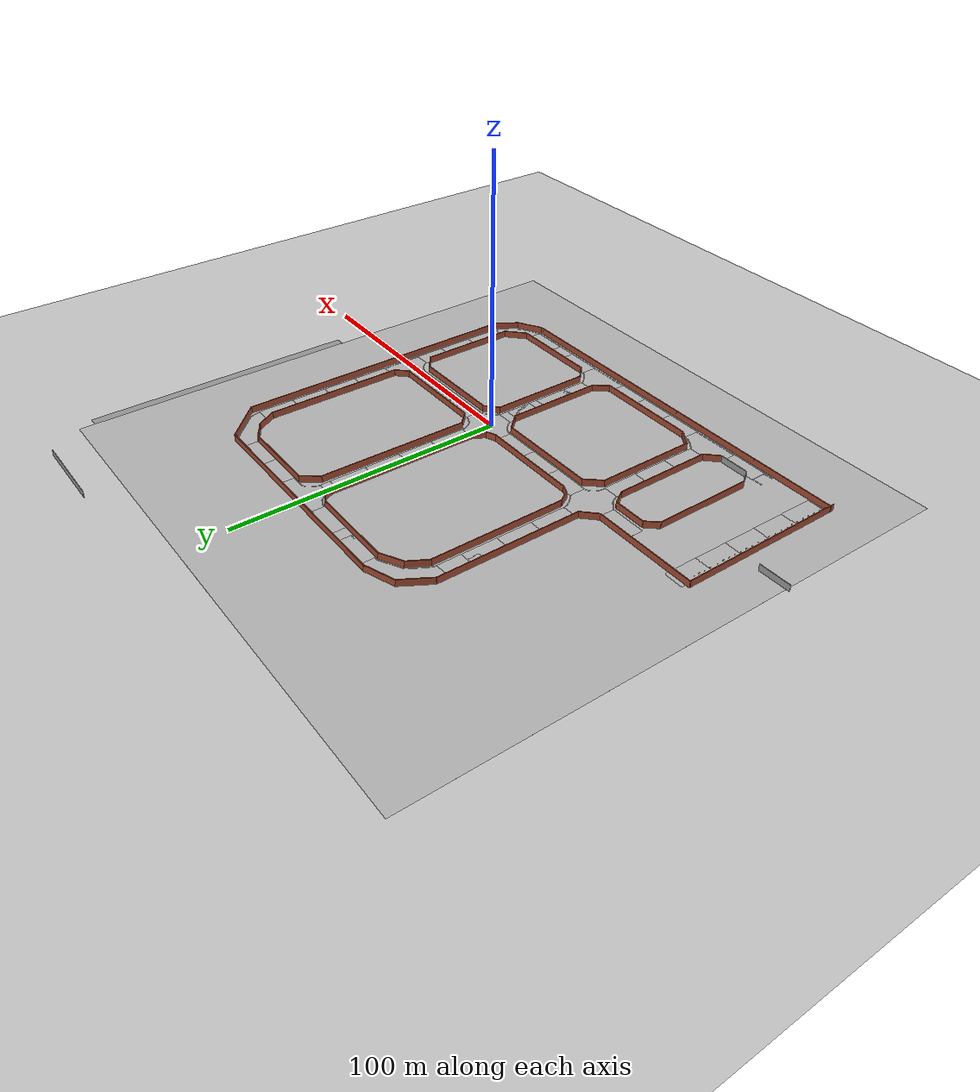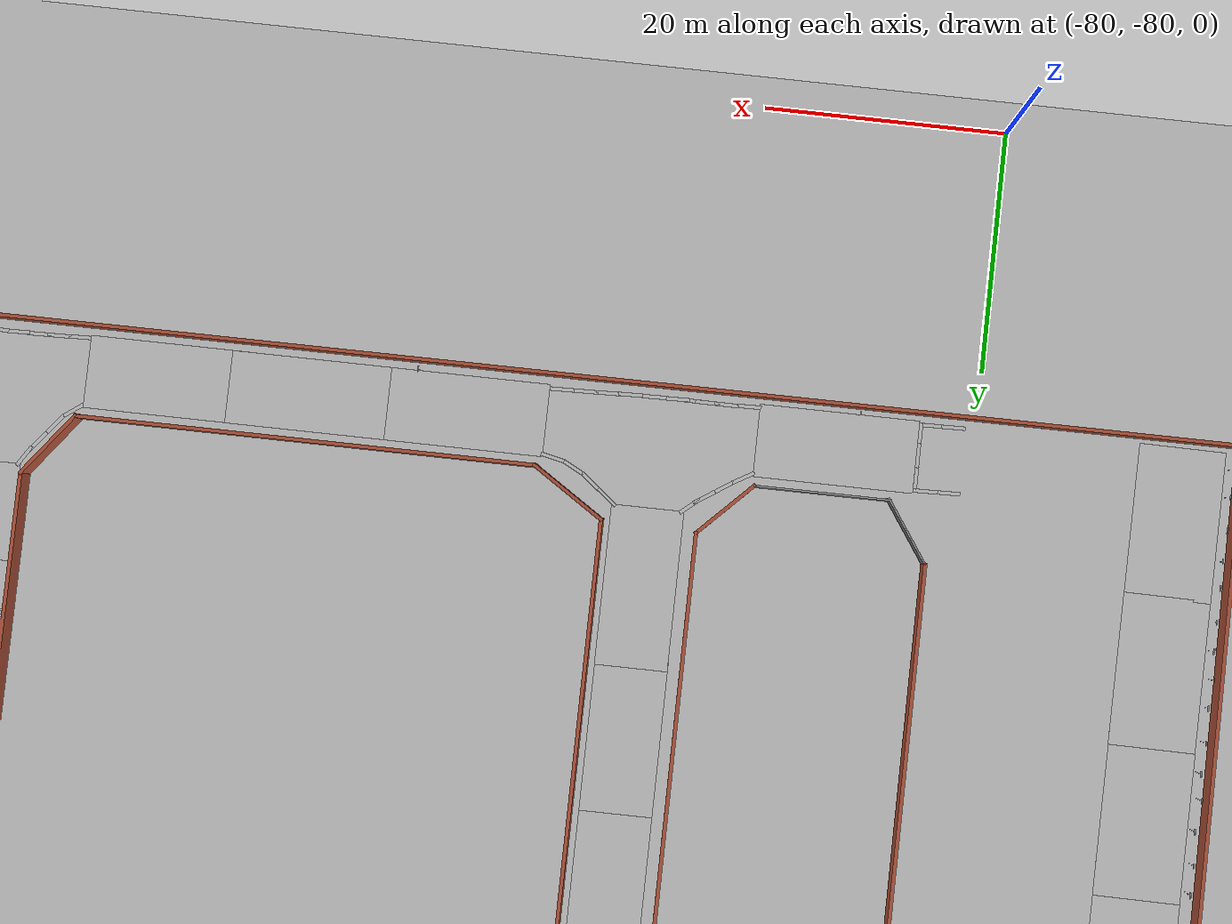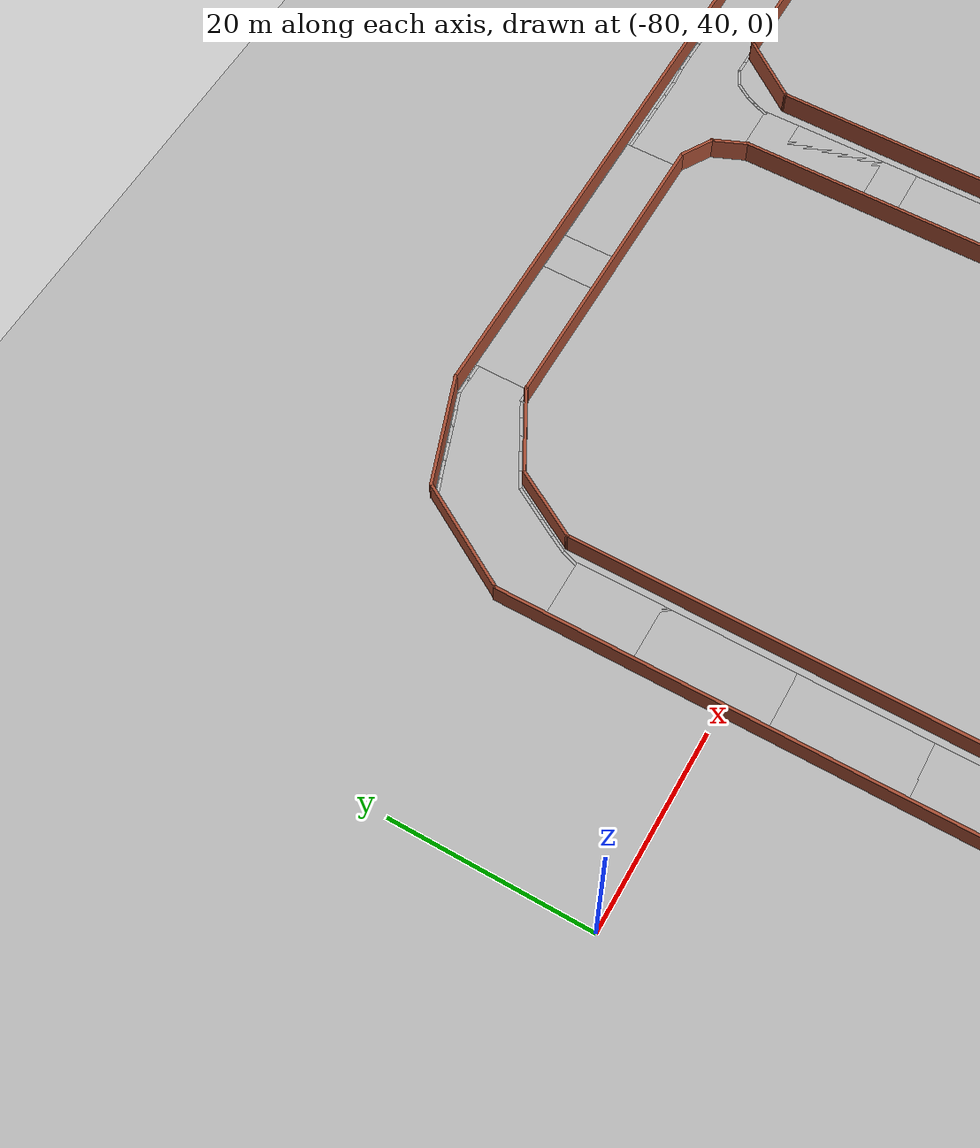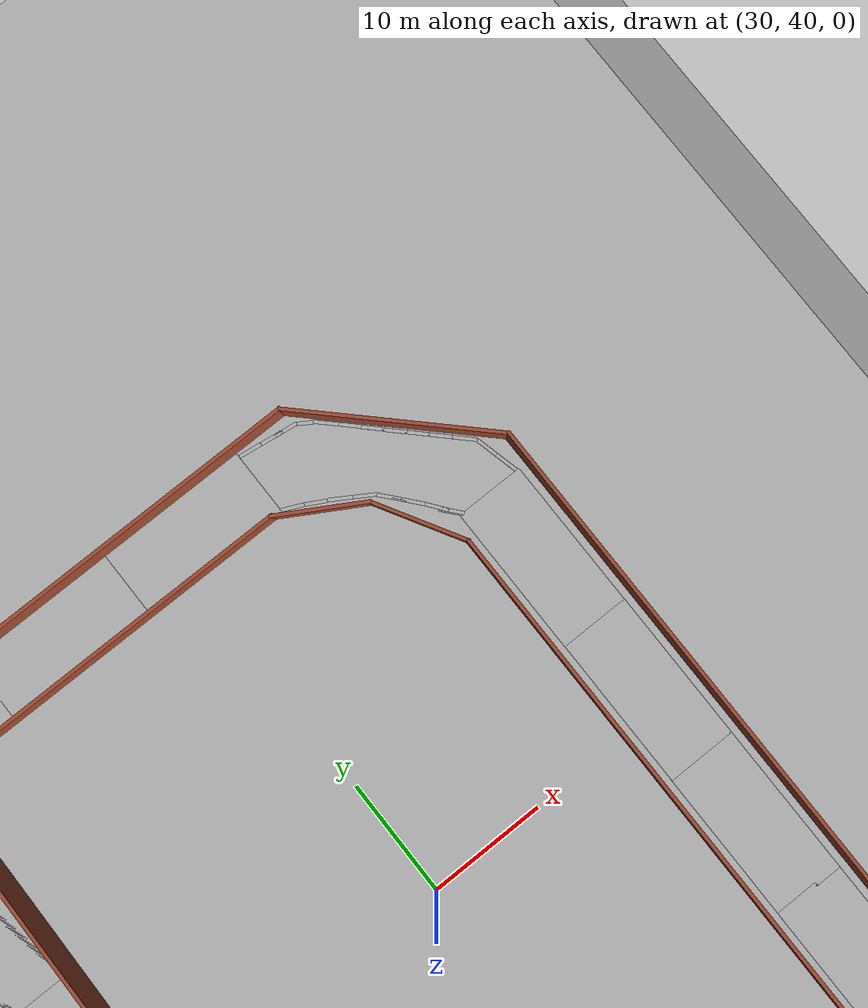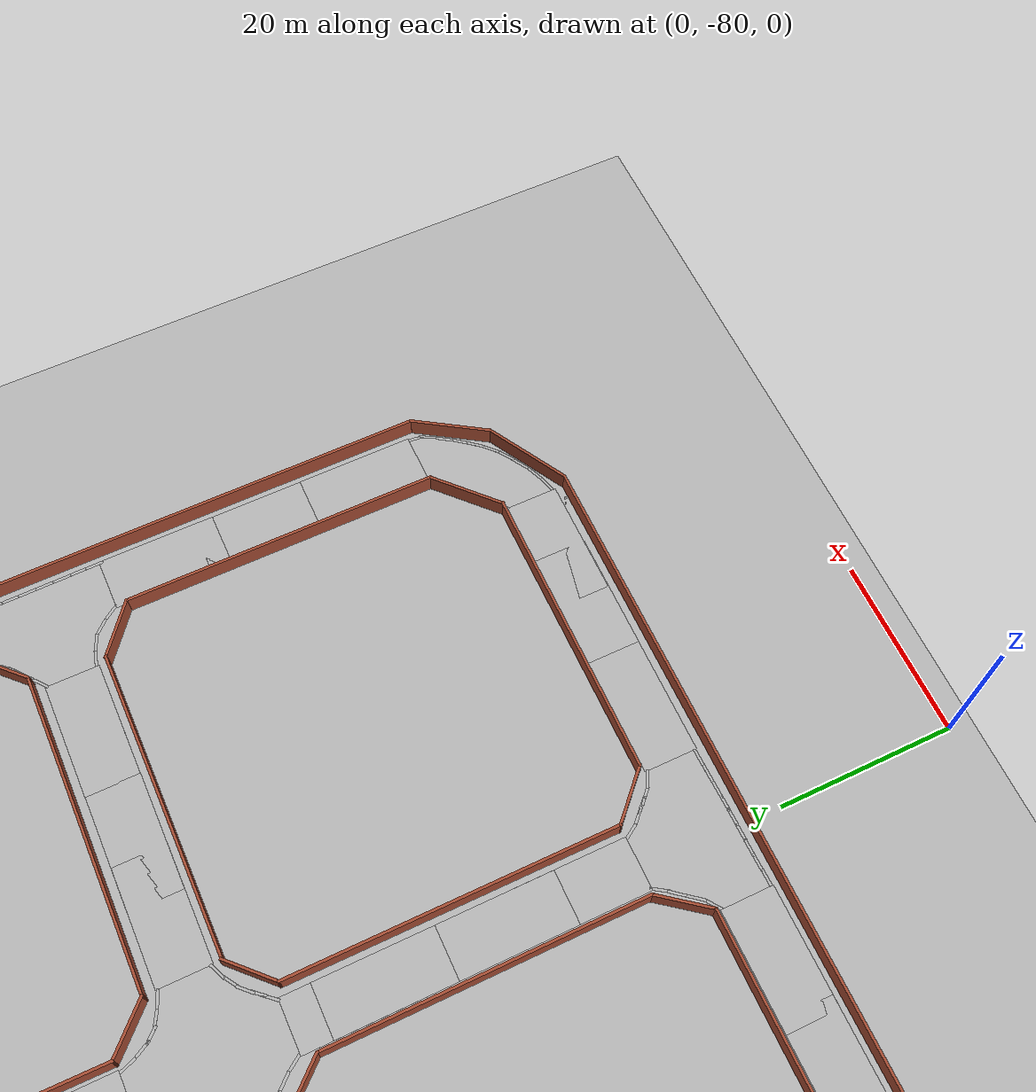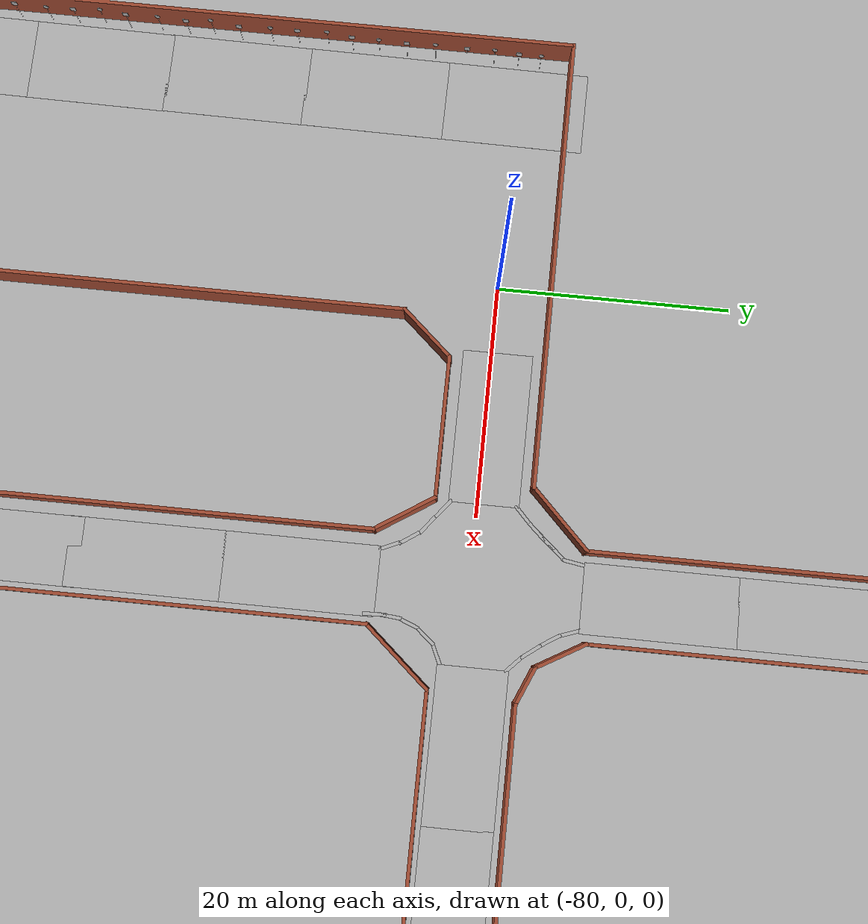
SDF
<sdf version="1.6">
 <world name="default">
  <light name="sun" type="directional">
   <pose>0 0 10 0 -0 0</pose>
   <diffuse>0.8 0.8 0.8 1</diffuse>
   <specular>0.2 0.2 0.2 1</specular>
   <attenuation>
    <range>1000</range>
    <constant>0.9</constant>
    <linear>0.01</linear>
    <quadratic>0.001</quadratic>
   </attenuation>
   <direction>-0.5 0.1 -0.9</direction>
  </light>
  <model name="ground_plane">
   <pose>0 0 -1 0 -0 0</pose>
   <static>1</static>
   <link name="link">
    <collision name="collision">
     <geometry><plane><normal>0 0 1</normal><size>100 100</size></plane></geometry>
     <surface><friction><ode><mu>100</mu><mu2>50</mu2></ode></friction></surface>
    </collision>
    <visual name="visual">
     <cast_shadows>0</cast_shadows>
     <geometry><plane><normal>0 0 1</normal><size>100 100</size></plane></geometry>
     <material>
      <script><uri>file://media/materials/scripts/gazebo.material</uri><name>Gazebo/Grey</name></script>
     </material>
    </visual>
   </link>
  </model>
  <gravity>0 0 -9.8</gravity>
  <magnetic_field>6e-06 2.3e-05 -4.2e-05</magnetic_field>
  <atmosphere type="adiabatic"/>
  <physics name="default_physics" default="0" type="ode">
   <max_step_size>0.001</max_step_size>
   <real_time_factor>1</real_time_factor>
   <real_time_update_rate>1000</real_time_update_rate>
  </physics>
  <scene><ambient>0.4 0.4 0.4 1</ambient><background>0.7 0.7 0.7 1</background><shadows>1</shadows></scene>
  <spherical_coordinates>
   <surface_model>EARTH_WGS84</surface_model>
   <latitude_deg>0</latitude_deg>
   <longitude_deg>0</longitude_deg>
   <elevation>0</elevation>
   <heading_deg>0</heading_deg>
  </spherical_coordinates>
  <model name="taksiYol">
   <pose>-24.3729 36.1774 0 0 -0 0</pose>
   <link name="Wall_10">
    <collision name="Wall_10_Collision">
     <geometry><box><size>18.0312 0.3 2.5</size></box></geometry>
     <pose>0 0 1.25 0 -0 0</pose>
    </collision>
    <visual name="Wall_10_Visual">
     <pose>0 0 1.25 0 -0 0</pose>
     <geometry><box><size>18.0312 0.3 2.5</size></box></geometry>
     <material>
      <script><uri>file://media/materials/scripts/gazebo.material</uri><name>Gazebo/Bricks</name></script>
      <ambient>0.760784 0.662745 0.627451 1</ambient>
     </material>
    </visual>
    <pose>74.2438 34.0389 0 0 0 -0.77802</pose>
   </link>
   <link name="Wall_100">
    <collision name="Wall_100_Collision">
     <geometry><box><size>28.6496 0.3 2.5</size></box></geometry>
     <pose>0 0 1.25 0 -0 0</pose>
    </collision>
    <visual name="Wall_100_Visual">
     <pose>0 0 1.25 0 -0 0</pose>
     <geometry><box><size>28.6496 0.3 2.5</size></box></geometry>
     <material>
      <script><uri>file://media/materials/scripts/gazebo.material</uri><name>Gazebo/Bricks</name></script>
      <ambient>0.760784 0.662745 0.627451 1</ambient>
     </material>
    </visual>
    <pose>48.1918 34.1744 0 0 -0 3.14068</pose>
   </link>
   <link name="Wall_102">
    <collision name="Wall_102_Collision">
     <geometry><box><size>6.3995 0.3 2.5</size></box></geometry>
     <pose>0 0 1.25 0 -0 0</pose>
    </collision>
    <visual name="Wall_102_Visual">
     <pose>0 0 1.25 0 -0 0</pose>
     <geometry><box><size>6.3995 0.3 2.5</size></box></geometry>
     <material>
      <script><uri>file://media/materials/scripts/gazebo.material</uri><name>Gazebo/Bricks</name></script>
      <ambient>0.760784 0.662745 0.627451 1</ambient>
     </material>
    </visual>
    <pose>-35.7537 -82.7531 0 0 -0 0.785398</pose>
   </link>
   <link name="Wall_103">
    <collision name="Wall_103_Collision">
     <geometry><box><size>36.349 0.3 2.5</size></box></geometry>
     <pose>0 0 1.25 0 -0 0</pose>
    </collision>
    <visual name="Wall_103_Visual">
     <pose>0 0 1.25 0 -0 0</pose>
     <geometry><box><size>36.349 0.3 2.5</size></box></geometry>
     <material>
      <script><uri>file://media/materials/scripts/gazebo.material</uri><name>Gazebo/Bricks</name></script>
      <ambient>0.760784 0.662745 0.627451 1</ambient>
     </material>
    </visual>
    <pose>-33.5972 -62.5721 0 0 -0 1.5708</pose>
   </link>
   <link name="Wall_104">
    <collision name="Wall_104_Collision">
     <geometry><box><size>6.02982 0.3 2.5</size></box></geometry>
     <pose>0 0 1.25 0 -0 0</pose>
    </collision>
    <visual name="Wall_104_Visual">
     <pose>0 0 1.25 0 -0 0</pose>
     <geometry><box><size>6.02982 0.3 2.5</size></box></geometry>
     <material>
      <script><uri>file://media/materials/scripts/gazebo.material</uri><name>Gazebo/Bricks</name></script>
      <ambient>0.760784 0.662745 0.627451 1</ambient>
     </material>
    </visual>
    <pose>-35.1517 -42.1411 0 0 -0 2.14432</pose>
   </link>
   <link name="Wall_106">
    <collision name="Wall_106_Collision">
     <geometry><box><size>12.2451 0.3 2.5</size></box></geometry>
     <pose>0 0 1.25 0 -0 0</pose>
    </collision>
    <visual name="Wall_106_Visual">
     <pose>0 0 1.25 0 -0 0</pose>
     <geometry><box><size>12.2451 0.3 2.5</size></box></geometry>
     <material>
      <script><uri>file://media/materials/scripts/gazebo.material</uri><name>Gazebo/Bricks</name></script>
      <ambient>0.760784 0.662745 0.627451 1</ambient>
     </material>
    </visual>
    <pose>-42.6787 -39.7341 0 0 0 -8.4e-05</pose>
   </link>
   <link name="Wall_19">
    <collision name="Wall_19_Collision">
     <geometry><box><size>144.415 0.3 2.5</size></box></geometry>
     <pose>0 0 1.25 0 -0 0</pose>
    </collision>
    <visual name="Wall_19_Visual">
     <pose>0 0 1.25 0 -0 0</pose>
     <geometry><box><size>144.415 0.3 2.5</size></box></geometry>
     <material>
      <script><uri>file://media/materials/scripts/gazebo.material</uri><name>Gazebo/Bricks</name></script>
      <ambient>0.760784 0.662745 0.627451 1</ambient>
     </material>
    </visual>
    <pose>-5.1646 -92.3029 0 0 0 -3.14128</pose>
   </link>
   <link name="Wall_2">
    <collision name="Wall_2_Collision">
     <geometry><box><size>62.289 0.3 2.5</size></box></geometry>
     <pose>0 0 1.25 0 -0 0</pose>
    </collision>
    <visual name="Wall_2_Visual">
     <pose>0 0 1.25 0 -0 0</pose>
     <geometry><box><size>62.289 0.3 2.5</size></box></geometry>
     <material>
      <script><uri>file://media/materials/scripts/gazebo.material</uri><name>Gazebo/Bricks</name></script>
      <ambient>0.760784 0.662745 0.627451 1</ambient>
     </material>
    </visual>
    <pose>-77.1823 -62.6861 0 0 -0 1.57079</pose>
   </link>
   <link name="Wall_20">
    <collision name="Wall_20_Collision">
     <geometry><box><size>0.388213 0.15 2.5</size></box></geometry>
     <pose>0 0 1.25 0 -0 0</pose>
    </collision>
    <visual name="Wall_20_Visual">
     <pose>0 0 1.25 0 -0 0</pose>
     <geometry><box><size>0.388213 0.15 2.5</size></box></geometry>
     <material>
      <script><uri>file://media/materials/scripts/gazebo.material</uri><name>Gazebo/Grey</name></script>
      <ambient>1 1 1 1</ambient>
     </material>
    </visual>
    <pose>-77.0291 -92.219 0 0 -0 1.10246</pose>
   </link>
   <link name="Wall_28">
    <collision name="Wall_28_Collision">
     <geometry><box><size>107.778 0.3 2.5</size></box></geometry>
     <pose>0 0 1.25 0 -0 0</pose>
    </collision>
    <visual name="Wall_28_Visual">
     <pose>0 0 1.25 0 -0 0</pose>
     <geometry><box><size>107.778 0.3 2.5</size></box></geometry>
     <material>
      <script><uri>file://media/materials/scripts/gazebo.material</uri><name>Gazebo/Bricks</name></script>
      <ambient>0.760784 0.662745 0.627451 1</ambient>
     </material>
    </visual>
    <pose>80.5423 -25.9226 0 0 -0 1.57049</pose>
   </link>
   <link name="Wall_30">
    <collision name="Wall_30_Collision">
     <geometry><box><size>12.1991 0.3 2.5</size></box></geometry>
     <pose>0 0 1.25 0 -0 0</pose>
    </collision>
    <visual name="Wall_30_Visual">
     <pose>0 0 1.25 0 -0 0</pose>
     <geometry><box><size>12.1991 0.3 2.5</size></box></geometry>
     <material>
      <script><uri>file://media/materials/scripts/gazebo.material</uri><name>Gazebo/Bricks</name></script>
      <ambient>0.760784 0.662745 0.627451 1</ambient>
     </material>
    </visual>
    <pose>-30.4626 31.2128 0 0 -0 1.03362</pose>
   </link>
   <link name="Wall_31">
    <collision name="Wall_31_Collision">
     <geometry><box><size>11.9805 0.3 2.5</size></box></geometry>
     <pose>0 0 1.25 0 -0 0</pose>
    </collision>
    <visual name="Wall_31_Visual">
     <pose>0 0 1.25 0 -0 0</pose>
     <geometry><box><size>11.9805 0.3 2.5</size></box></geometry>
     <material>
      <script><uri>file://media/materials/scripts/gazebo.material</uri><name>Gazebo/Bricks</name></script>
      <ambient>0.760784 0.662745 0.627451 1</ambient>
     </material>
    </visual>
    <pose>-21.9197 38.2929 0 0 -0 0.34379</pose>
   </link>
   <link name="Wall_33">
    <collision name="Wall_33_Collision">
     <geometry><box><size>31.9 0.3 2.5</size></box></geometry>
     <pose>0 0 1.25 0 -0 0</pose>
    </collision>
    <visual name="Wall_33_Visual">
     <pose>0 0 1.25 0 -0 0</pose>
     <geometry><box><size>31.9 0.3 2.5</size></box></geometry>
     <material>
      <script><uri>file://media/materials/scripts/gazebo.material</uri><name>Gazebo/Bricks</name></script>
      <ambient>0.760784 0.662745 0.627451 1</ambient>
     </material>
    </visual>
    <pose>1.55483 33.8794 0 0 -0 0</pose>
   </link>
   <link name="Wall_34">
    <collision name="Wall_34_Collision">
     <geometry><box><size>3.8606 0.3 2.5</size></box></geometry>
     <pose>0 0 1.25 0 -0 0</pose>
    </collision>
    <visual name="Wall_34_Visual">
     <pose>0 0 1.25 0 -0 0</pose>
     <geometry><box><size>3.8606 0.3 2.5</size></box></geometry>
     <material>
      <script><uri>file://media/materials/scripts/gazebo.material</uri><name>Gazebo/Bricks</name></script>
      <ambient>0.760784 0.662745 0.627451 1</ambient>
     </material>
    </visual>
    <pose>18.8908 32.9794 0 0 0 -0.530015</pose>
   </link>
   <link name="Wall_35">
    <collision name="Wall_35_Collision">
     <geometry><box><size>3.92162 0.3 2.5</size></box></geometry>
     <pose>0 0 1.25 0 -0 0</pose>
    </collision>
    <visual name="Wall_35_Visual">
     <pose>0 0 1.25 0 -0 0</pose>
     <geometry><box><size>3.92162 0.3 2.5</size></box></geometry>
     <material>
      <script><uri>file://media/materials/scripts/gazebo.material</uri><name>Gazebo/Bricks</name></script>
      <ambient>0.760784 0.662745 0.627451 1</ambient>
     </material>
    </visual>
    <pose>21.1248 30.4084 0 0 0 -1.17511</pose>
   </link>
   <link name="Wall_36">
    <collision name="Wall_36_Collision">
     <geometry><box><size>55.1498 0.3 2.5</size></box></geometry>
     <pose>0 0 1.25 0 -0 0</pose>
    </collision>
    <visual name="Wall_36_Visual">
     <pose>0 0 1.25 0 -0 0</pose>
     <geometry><box><size>55.1498 0.3 2.5</size></box></geometry>
     <material>
      <script><uri>file://media/materials/scripts/gazebo.material</uri><name>Gazebo/Bricks</name></script>
      <ambient>0.760784 0.662745 0.627451 1</ambient>
     </material>
    </visual>
    <pose>21.7828 1.3124 0 0 0 -1.57225</pose>
   </link>
   <link name="Wall_37">
    <collision name="Wall_37_Collision">
     <geometry><box><size>4.90024 0.3 2.5</size></box></geometry>
     <pose>0 0 1.25 0 -0 0</pose>
    </collision>
    <visual name="Wall_37_Visual">
     <pose>0 0 1.25 0 -0 0</pose>
     <geometry><box><size>4.90024 0.3 2.5</size></box></geometry>
     <material>
      <script><uri>file://media/materials/scripts/gazebo.material</uri><name>Gazebo/Bricks</name></script>
      <ambient>0.760784 0.662745 0.627451 1</ambient>
     </material>
    </visual>
    <pose>20.5928 -28.1046 0 0 0 -2.09436</pose>
   </link>
   <link name="Wall_38">
    <collision name="Wall_38_Collision">
     <geometry><box><size>4.21544 0.3 2.5</size></box></geometry>
     <pose>0 0 1.25 0 -0 0</pose>
    </collision>
    <visual name="Wall_38_Visual">
     <pose>0 0 1.25 0 -0 0</pose>
     <geometry><box><size>4.21544 0.3 2.5</size></box></geometry>
     <material>
      <script><uri>file://media/materials/scripts/gazebo.material</uri><name>Gazebo/Bricks</name></script>
      <ambient>0.760784 0.662745 0.627451 1</ambient>
     </material>
    </visual>
    <pose>17.6418 -30.8641 0 0 0 -2.73875</pose>
   </link>
   <link name="Wall_39">
    <collision name="Wall_39_Collision">
     <geometry><box><size>36.6502 0.3 2.5</size></box></geometry>
     <pose>0 0 1.25 0 -0 0</pose>
    </collision>
    <visual name="Wall_39_Visual">
     <pose>0 0 1.25 0 -0 0</pose>
     <geometry><box><size>36.6502 0.3 2.5</size></box></geometry>
     <material>
      <script><uri>file://media/materials/scripts/gazebo.material</uri><name>Gazebo/Bricks</name></script>
      <ambient>0.760784 0.662745 0.627451 1</ambient>
     </material>
    </visual>
    <pose>-2.33417 -31.6316 0 0 -0 3.14159</pose>
   </link>
   <link name="Wall_40">
    <collision name="Wall_40_Collision">
     <geometry><box><size>3.68766 0.3 2.5</size></box></geometry>
     <pose>0 0 1.25 0 -0 0</pose>
    </collision>
    <visual name="Wall_40_Visual">
     <pose>0 0 1.25 0 -0 0</pose>
     <geometry><box><size>3.68766 0.3 2.5</size></box></geometry>
     <material>
      <script><uri>file://media/materials/scripts/gazebo.material</uri><name>Gazebo/Bricks</name></script>
      <ambient>0.760784 0.662745 0.627451 1</ambient>
     </material>
    </visual>
    <pose>-22.0652 -30.9621 0 0 -0 2.73527</pose>
   </link>
   <link name="Wall_41">
    <collision name="Wall_41_Collision">
     <geometry><box><size>4.90013 0.3 2.5</size></box></geometry>
     <pose>0 0 1.25 0 -0 0</pose>
    </collision>
    <visual name="Wall_41_Visual">
     <pose>0 0 1.25 0 -0 0</pose>
     <geometry><box><size>4.90013 0.3 2.5</size></box></geometry>
     <material>
      <script><uri>file://media/materials/scripts/gazebo.material</uri><name>Gazebo/Bricks</name></script>
      <ambient>0.760784 0.662745 0.627451 1</ambient>
     </material>
    </visual>
    <pose>-24.7712 -28.3006 0 0 -0 2.09436</pose>
   </link>
   <link name="Wall_42">
    <collision name="Wall_42_Collision">
     <geometry><box><size>49.6501 0.3 2.5</size></box></geometry>
     <pose>0 0 1.25 0 -0 0</pose>
    </collision>
    <visual name="Wall_42_Visual">
     <pose>0 0 1.25 0 -0 0</pose>
     <geometry><box><size>49.6501 0.3 2.5</size></box></geometry>
     <material>
      <script><uri>file://media/materials/scripts/gazebo.material</uri><name>Gazebo/Bricks</name></script>
      <ambient>0.760784 0.662745 0.627451 1</ambient>
     </material>
    </visual>
    <pose>-25.9212 -1.6336 0 0 -0 1.5708</pose>
   </link>
   <link name="Wall_43">
    <collision name="Wall_43_Collision">
     <geometry><box><size>7.90018 0.3 2.5</size></box></geometry>
     <pose>0 0 1.25 0 -0 0</pose>
    </collision>
    <visual name="Wall_43_Visual">
     <pose>0 0 1.25 0 -0 0</pose>
     <geometry><box><size>7.90018 0.3 2.5</size></box></geometry>
     <material>
      <script><uri>file://media/materials/scripts/gazebo.material</uri><name>Gazebo/Bricks</name></script>
      <ambient>0.760784 0.662745 0.627451 1</ambient>
     </material>
    </visual>
    <pose>-24.0212 26.3324 0 0 -0 1.04721</pose>
   </link>
   <link name="Wall_44">
    <collision name="Wall_44_Collision">
     <geometry><box><size>9.25237 0.3 2.5</size></box></geometry>
     <pose>0 0 1.25 0 -0 0</pose>
    </collision>
    <visual name="Wall_44_Visual">
     <pose>0 0 1.25 0 -0 0</pose>
     <geometry><box><size>9.25237 0.3 2.5</size></box></geometry>
     <material>
      <script><uri>file://media/materials/scripts/gazebo.material</uri><name>Gazebo/Bricks</name></script>
      <ambient>0.760784 0.662745 0.627451 1</ambient>
     </material>
    </visual>
    <pose>-18.1832 31.7514 0 0 -0 0.495424</pose>
   </link>
   <link name="Wall_48">
    <collision name="Wall_48_Collision">
     <geometry><box><size>11.7505 0.15 2.5</size></box></geometry>
     <pose>0 0 1.25 0 -0 0</pose>
    </collision>
    <visual name="Wall_48_Visual">
     <pose>0 0 1.25 0 -0 0</pose>
     <geometry><box><size>11.7505 0.15 2.5</size></box></geometry>
     <material>
      <script><uri>file://media/materials/scripts/gazebo.material</uri><name>Gazebo/Grey</name></script>
      <ambient>1 1 1 1</ambient>
     </material>
    </visual>
    <pose>-89.3267 -53.5426 0 0 -0 0.008844</pose>
   </link>
   <link name="Wall_52">
    <collision name="Wall_52_Collision">
     <geometry><box><size>11.25 0.15 2.5</size></box></geometry>
     <pose>0 0 1.25 0 -0 0</pose>
    </collision>
    <visual name="Wall_52_Visual">
     <pose>0 0 1.25 0 -0 0</pose>
     <geometry><box><size>11.25 0.15 2.5</size></box></geometry>
     <material>
      <script><uri>file://media/materials/scripts/gazebo.material</uri><name>Gazebo/Grey</name></script>
      <ambient>1 1 1 1</ambient>
     </material>
    </visual>
    <pose>-43.4601 -84.9096 0 0 0 -3.14159</pose>
   </link>
   <link name="Wall_53">
    <collision name="Wall_53_Collision">
     <geometry><box><size>6.25105 0.15 2.5</size></box></geometry>
     <pose>0 0 1.25 0 -0 0</pose>
    </collision>
    <visual name="Wall_53_Visual">
     <pose>0 0 1.25 0 -0 0</pose>
     <geometry><box><size>6.25105 0.15 2.5</size></box></geometry>
     <material>
      <script><uri>file://media/materials/scripts/gazebo.material</uri><name>Gazebo/Grey</name></script>
      <ambient>1 1 1 1</ambient>
     </material>
    </visual>
    <pose>-50.6298 -82.4944 0 0 -0 2.17074</pose>
   </link>
   <link name="Wall_54">
    <collision name="Wall_54_Collision">
     <geometry><box><size>36.4 0.3 2.5</size></box></geometry>
     <pose>0 0 1.25 0 -0 0</pose>
    </collision>
    <visual name="Wall_54_Visual">
     <pose>0 0 1.25 0 -0 0</pose>
     <geometry><box><size>36.4 0.3 2.5</size></box></geometry>
     <material>
      <script><uri>file://media/materials/scripts/gazebo.material</uri><name>Gazebo/Bricks</name></script>
      <ambient>0.760784 0.662745 0.627451 1</ambient>
     </material>
    </visual>
    <pose>-52.3522 -61.9266 0 0 -0 1.5708</pose>
   </link>
   <link name="Wall_55">
    <collision name="Wall_55_Collision">
     <geometry><box><size>5.85534 0.3 2.5</size></box></geometry>
     <pose>0 0 1.25 0 -0 0</pose>
    </collision>
    <visual name="Wall_55_Visual">
     <pose>0 0 1.25 0 -0 0</pose>
     <geometry><box><size>5.85534 0.3 2.5</size></box></geometry>
     <material>
      <script><uri>file://media/materials/scripts/gazebo.material</uri><name>Gazebo/Bricks</name></script>
      <ambient>0.760784 0.662745 0.627451 1</ambient>
     </material>
    </visual>
    <pose>-50.5017 -41.8051 0 0 -0 0.841687</pose>
   </link>
   <link name="Wall_57">
    <collision name="Wall_57_Collision">
     <geometry><box><size>37.9 0.3 2.5</size></box></geometry>
     <pose>0 0 1.25 0 -0 0</pose>
    </collision>
    <visual name="Wall_57_Visual">
     <pose>0 0 1.25 0 -0 0</pose>
     <geometry><box><size>37.9 0.3 2.5</size></box></geometry>
     <material>
      <script><uri>file://media/materials/scripts/gazebo.material</uri><name>Gazebo/Bricks</name></script>
      <ambient>0.760784 0.662745 0.627451 1</ambient>
     </material>
    </visual>
    <pose>-2.17517 -38.8776 0 0 -0 0</pose>
   </link>
   <link name="Wall_58">
    <collision name="Wall_58_Collision">
     <geometry><box><size>7.63118 0.3 2.5</size></box></geometry>
     <pose>0 0 1.25 0 -0 0</pose>
    </collision>
    <visual name="Wall_58_Visual">
     <pose>0 0 1.25 0 -0 0</pose>
     <geometry><box><size>7.63118 0.3 2.5</size></box></geometry>
     <material>
      <script><uri>file://media/materials/scripts/gazebo.material</uri><name>Gazebo/Bricks</name></script>
      <ambient>0.760784 0.662745 0.627451 1</ambient>
     </material>
    </visual>
    <pose>19.0648 -41.6131 0 0 0 -0.842432</pose>
   </link>
   <link name="Wall_59">
    <collision name="Wall_59_Collision">
     <geometry><box><size>35.65 0.3 2.5</size></box></geometry>
     <pose>0 0 1.25 0 -0 0</pose>
    </collision>
    <visual name="Wall_59_Visual">
     <pose>0 0 1.25 0 -0 0</pose>
     <geometry><box><size>35.65 0.3 2.5</size></box></geometry>
     <material>
      <script><uri>file://media/materials/scripts/gazebo.material</uri><name>Gazebo/Bricks</name></script>
      <ambient>0.760784 0.662745 0.627451 1</ambient>
     </material>
    </visual>
    <pose>21.5048 -62.0236 0 0 0 -1.5708</pose>
   </link>
   <link name="Wall_60">
    <collision name="Wall_60_Collision">
     <geometry><box><size>6.64794 0.3 2.5</size></box></geometry>
     <pose>0 0 1.25 0 -0 0</pose>
    </collision>
    <visual name="Wall_60_Visual">
     <pose>0 0 1.25 0 -0 0</pose>
     <geometry><box><size>6.64794 0.3 2.5</size></box></geometry>
     <material>
      <script><uri>file://media/materials/scripts/gazebo.material</uri><name>Gazebo/Bricks</name></script>
      <ambient>0.760784 0.662745 0.627451 1</ambient>
     </material>
    </visual>
    <pose>19.5738 -82.2176 0 0 0 -2.22482</pose>
   </link>
   <link name="Wall_61">
    <collision name="Wall_61_Collision">
     <geometry><box><size>37.8997 0.3 2.5</size></box></geometry>
     <pose>0 0 1.25 0 -0 0</pose>
    </collision>
    <visual name="Wall_61_Visual">
     <pose>0 0 1.25 0 -0 0</pose>
     <geometry><box><size>37.8997 0.3 2.5</size></box></geometry>
     <material>
      <script><uri>file://media/materials/scripts/gazebo.material</uri><name>Gazebo/Bricks</name></script>
      <ambient>0.760784 0.662745 0.627451 1</ambient>
     </material>
    </visual>
    <pose>-1.15717 -84.7166 0 0 -0 3.14053</pose>
   </link>
   <link name="Wall_62">
    <collision name="Wall_62_Collision">
     <geometry><box><size>7.28015 0.3 2.5</size></box></geometry>
     <pose>0 0 1.25 0 -0 0</pose>
    </collision>
    <visual name="Wall_62_Visual">
     <pose>0 0 1.25 0 -0 0</pose>
     <geometry><box><size>7.28015 0.3 2.5</size></box></geometry>
     <material>
      <script><uri>file://media/materials/scripts/gazebo.material</uri><name>Gazebo/Bricks</name></script>
      <ambient>0.760784 0.662745 0.627451 1</ambient>
     </material>
    </visual>
    <pose>-22.8797 -82.7886 0 0 -0 2.56321</pose>
   </link>
   <link name="Wall_63">
    <collision name="Wall_63_Collision">
     <geometry><box><size>36.8614 0.3 2.5</size></box></geometry>
     <pose>0 0 1.25 0 -0 0</pose>
    </collision>
    <visual name="Wall_63_Visual">
     <pose>0 0 1.25 0 -0 0</pose>
     <geometry><box><size>36.8614 0.3 2.5</size></box></geometry>
     <material>
      <script><uri>file://media/materials/scripts/gazebo.material</uri><name>Gazebo/Bricks</name></script>
      <ambient>0.760784 0.662745 0.627451 1</ambient>
     </material>
    </visual>
    <pose>-25.8022 -62.6001 0 0 -0 1.5708</pose>
   </link>
   <link name="Wall_64">
    <collision name="Wall_64_Collision">
     <geometry><box><size>7.49247 0.3 2.5</size></box></geometry>
     <pose>0 0 1.25 0 -0 0</pose>
    </collision>
    <visual name="Wall_64_Visual">
     <pose>0 0 1.25 0 -0 0</pose>
     <geometry><box><size>7.49247 0.3 2.5</size></box></geometry>
     <material>
      <script><uri>file://media/materials/scripts/gazebo.material</uri><name>Gazebo/Bricks</name></script>
      <ambient>0.760784 0.662745 0.627451 1</ambient>
     </material>
    </visual>
    <pose>-23.4307 -41.6161 0 0 -0 0.850724</pose>
   </link>
   <link name="Wall_69">
    <collision name="Wall_69_Collision">
     <geometry><box><size>39.15 0.3 2.5</size></box></geometry>
     <pose>0 0 1.25 0 -0 0</pose>
    </collision>
    <visual name="Wall_69_Visual">
     <pose>0 0 1.25 0 -0 0</pose>
     <geometry><box><size>39.15 0.3 2.5</size></box></geometry>
     <material>
      <script><uri>file://media/materials/scripts/gazebo.material</uri><name>Gazebo/Bricks</name></script>
      <ambient>0.760784 0.662745 0.627451 1</ambient>
     </material>
    </visual>
    <pose>-57.7572 -31.6916 0 0 -0 0</pose>
   </link>
   <link name="Wall_70">
    <collision name="Wall_70_Collision">
     <geometry><box><size>7.12222 0.3 2.5</size></box></geometry>
     <pose>0 0 1.25 0 -0 0</pose>
    </collision>
    <visual name="Wall_70_Visual">
     <pose>0 0 1.25 0 -0 0</pose>
     <geometry><box><size>7.12222 0.3 2.5</size></box></geometry>
     <material>
      <script><uri>file://media/materials/scripts/gazebo.material</uri><name>Gazebo/Bricks</name></script>
      <ambient>0.760784 0.662745 0.627451 1</ambient>
     </material>
    </visual>
    <pose>-35.9107 -29.2891 0 0 -0 0.78146</pose>
   </link>
   <link name="Wall_72">
    <collision name="Wall_72_Collision">
     <geometry><box><size>53.2861 0.3 2.5</size></box></geometry>
     <pose>0 0 1.25 0 -0 0</pose>
    </collision>
    <visual name="Wall_72_Visual">
     <pose>0 0 1.25 0 -0 0</pose>
     <geometry><box><size>53.2861 0.3 2.5</size></box></geometry>
     <material>
      <script><uri>file://media/materials/scripts/gazebo.material</uri><name>Gazebo/Bricks</name></script>
      <ambient>0.760784 0.662745 0.627451 1</ambient>
     </material>
    </visual>
    <pose>-33.5187 -0.393597 0 0 -0 1.57191</pose>
   </link>
   <link name="Wall_73">
    <collision name="Wall_73_Collision">
     <geometry><box><size>0.181339 0.15 2.5</size></box></geometry>
     <pose>0 0 1.25 0 -0 0</pose>
    </collision>
    <visual name="Wall_73_Visual">
     <pose>0 0 1.25 0 -0 0</pose>
     <geometry><box><size>0.181339 0.15 2.5</size></box></geometry>
     <material>
      <script><uri>file://media/materials/scripts/gazebo.material</uri><name>Gazebo/Grey</name></script>
      <ambient>1 1 1 1</ambient>
     </material>
    </visual>
    <pose>-33.5434 26.0845 0 0 0 -1.25908</pose>
   </link>
   <link name="Wall_75">
    <collision name="Wall_75_Collision">
     <geometry><box><size>34.6499 0.3 2.5</size></box></geometry>
     <pose>0 0 1.25 0 -0 0</pose>
    </collision>
    <visual name="Wall_75_Visual">
     <pose>0 0 1.25 0 -0 0</pose>
     <geometry><box><size>34.6499 0.3 2.5</size></box></geometry>
     <material>
      <script><uri>file://media/materials/scripts/gazebo.material</uri><name>Gazebo/Bricks</name></script>
      <ambient>0.760784 0.662745 0.627451 1</ambient>
     </material>
    </visual>
    <pose>50.6358 -39.2886 0 0 -0 0</pose>
   </link>
   <link name="Wall_76">
    <collision name="Wall_76_Collision">
     <geometry><box><size>6.94108 0.3 2.5</size></box></geometry>
     <pose>0 0 1.25 0 -0 0</pose>
    </collision>
    <visual name="Wall_76_Visual">
     <pose>0 0 1.25 0 -0 0</pose>
     <geometry><box><size>6.94108 0.3 2.5</size></box></geometry>
     <material>
      <script><uri>file://media/materials/scripts/gazebo.material</uri><name>Gazebo/Bricks</name></script>
      <ambient>0.760784 0.662745 0.627451 1</ambient>
     </material>
    </visual>
    <pose>70.4218 -41.3401 0 0 0 -0.665969</pose>
   </link>
   <link name="Wall_77">
    <collision name="Wall_77_Collision">
     <geometry><box><size>35.65 0.3 2.5</size></box></geometry>
     <pose>0 0 1.25 0 -0 0</pose>
    </collision>
    <visual name="Wall_77_Visual">
     <pose>0 0 1.25 0 -0 0</pose>
     <geometry><box><size>35.65 0.3 2.5</size></box></geometry>
     <material>
      <script><uri>file://media/materials/scripts/gazebo.material</uri><name>Gazebo/Bricks</name></script>
      <ambient>0.760784 0.662745 0.627451 1</ambient>
     </material>
    </visual>
    <pose>73.0328 -61.0666 0 0 0 -1.5708</pose>
   </link>
   <link name="Wall_78">
    <collision name="Wall_78_Collision">
     <geometry><box><size>8.98794 0.3 2.5</size></box></geometry>
     <pose>0 0 1.25 0 -0 0</pose>
    </collision>
    <visual name="Wall_78_Visual">
     <pose>0 0 1.25 0 -0 0</pose>
     <geometry><box><size>8.98794 0.3 2.5</size></box></geometry>
     <material>
      <script><uri>file://media/materials/scripts/gazebo.material</uri><name>Gazebo/Bricks</name></script>
      <ambient>0.760784 0.662745 0.627451 1</ambient>
     </material>
    </visual>
    <pose>69.8698 -81.7191 0 0 0 -2.38639</pose>
   </link>
   <link name="Wall_79">
    <collision name="Wall_79_Collision">
     <geometry><box><size>33.225 0.3 2.5</size></box></geometry>
     <pose>0 0 1.25 0 -0 0</pose>
    </collision>
    <visual name="Wall_79_Visual">
     <pose>0 0 1.25 0 -0 0</pose>
     <geometry><box><size>33.225 0.3 2.5</size></box></geometry>
     <material>
      <script><uri>file://media/materials/scripts/gazebo.material</uri><name>Gazebo/Bricks</name></script>
      <ambient>0.760784 0.662745 0.627451 1</ambient>
     </material>
    </visual>
    <pose>50.2443 -84.6666 0 0 -0 3.13977</pose>
   </link>
   <link name="Wall_80">
    <collision name="Wall_80_Collision">
     <geometry><box><size>6.88701 0.3 2.5</size></box></geometry>
     <pose>0 0 1.25 0 -0 0</pose>
    </collision>
    <visual name="Wall_80_Visual">
     <pose>0 0 1.25 0 -0 0</pose>
     <geometry><box><size>6.88701 0.3 2.5</size></box></geometry>
     <material>
      <script><uri>file://media/materials/scripts/gazebo.material</uri><name>Gazebo/Bricks</name></script>
      <ambient>0.760784 0.662745 0.627451 1</ambient>
     </material>
    </visual>
    <pose>31.4123 -82.3491 0 0 -0 2.3738</pose>
   </link>
   <link name="Wall_81">
    <collision name="Wall_81_Collision">
     <geometry><box><size>36.867 0.3 2.5</size></box></geometry>
     <pose>0 0 1.25 0 -0 0</pose>
    </collision>
    <visual name="Wall_81_Visual">
     <pose>0 0 1.25 0 -0 0</pose>
     <geometry><box><size>36.867 0.3 2.5</size></box></geometry>
     <material>
      <script><uri>file://media/materials/scripts/gazebo.material</uri><name>Gazebo/Bricks</name></script>
      <ambient>0.760784 0.662745 0.627451 1</ambient>
     </material>
    </visual>
    <pose>29.0728 -61.7781 0 0 -0 1.56916</pose>
   </link>
   <link name="Wall_82">
    <collision name="Wall_82_Collision">
     <geometry><box><size>6.36848 0.3 2.5</size></box></geometry>
     <pose>0 0 1.25 0 -0 0</pose>
    </collision>
    <visual name="Wall_82_Visual">
     <pose>0 0 1.25 0 -0 0</pose>
     <geometry><box><size>6.36848 0.3 2.5</size></box></geometry>
     <material>
      <script><uri>file://media/materials/scripts/gazebo.material</uri><name>Gazebo/Bricks</name></script>
      <ambient>0.760784 0.662745 0.627451 1</ambient>
     </material>
    </visual>
    <pose>31.2598 -41.3606 0 0 -0 0.780038</pose>
   </link>
   <link name="Wall_86">
    <collision name="Wall_86_Collision">
     <geometry><box><size>29 0.15 2.5</size></box></geometry>
     <pose>0 0 1.25 0 -0 0</pose>
    </collision>
    <visual name="Wall_86_Visual">
     <pose>0 0 1.25 0 -0 0</pose>
     <geometry><box><size>29 0.15 2.5</size></box></geometry>
     <material>
      <script><uri>file://media/materials/scripts/gazebo.material</uri><name>Gazebo/Grey</name></script>
      <ambient>1 1 1 1</ambient>
     </material>
    </visual>
    <pose>80.7024 93.7556 0 0 -0 0</pose>
   </link>
   <link name="Wall_88">
    <collision name="Wall_88_Collision">
     <geometry><box><size>8.4071 0.3 2.5</size></box></geometry>
     <pose>0 0 1.25 0 -0 0</pose>
    </collision>
    <visual name="Wall_88_Visual">
     <pose>0 0 1.25 0 -0 0</pose>
     <geometry><box><size>8.4071 0.3 2.5</size></box></geometry>
     <material>
      <script><uri>file://media/materials/scripts/gazebo.material</uri><name>Gazebo/Bricks</name></script>
      <ambient>0.760784 0.662745 0.627451 1</ambient>
     </material>
    </visual>
    <pose>70.9738 26.8239 0 0 0 -1.0477</pose>
   </link>
   <link name="Wall_89">
    <collision name="Wall_89_Collision">
     <geometry><box><size>50.874 0.3 2.5</size></box></geometry>
     <pose>0 0 1.25 0 -0 0</pose>
    </collision>
    <visual name="Wall_89_Visual">
     <pose>0 0 1.25 0 -0 0</pose>
     <geometry><box><size>50.874 0.3 2.5</size></box></geometry>
     <material>
      <script><uri>file://media/materials/scripts/gazebo.material</uri><name>Gazebo/Bricks</name></script>
      <ambient>0.760784 0.662745 0.627451 1</ambient>
     </material>
    </visual>
    <pose>72.9988 -1.9746 0 0 0 -1.5708</pose>
   </link>
   <link name="Wall_9">
    <collision name="Wall_9_Collision">
     <geometry><box><size>84.65 0.3 2.5</size></box></geometry>
     <pose>0 0 1.25 0 -0 0</pose>
    </collision>
    <visual name="Wall_9_Visual">
     <pose>0 0 1.25 0 -0 0</pose>
     <geometry><box><size>84.65 0.3 2.5</size></box></geometry>
     <material>
      <script><uri>file://media/materials/scripts/gazebo.material</uri><name>Gazebo/Bricks</name></script>
      <ambient>0.760784 0.662745 0.627451 1</ambient>
     </material>
    </visual>
    <pose>25.7538 40.2614 0 0 -0 0</pose>
   </link>
   <link name="Wall_90">
    <collision name="Wall_90_Collision">
     <geometry><box><size>5.8763 0.3 2.5</size></box></geometry>
     <pose>0 0 1.25 0 -0 0</pose>
    </collision>
    <visual name="Wall_90_Visual">
     <pose>0 0 1.25 0 -0 0</pose>
     <geometry><box><size>5.8763 0.3 2.5</size></box></geometry>
     <material>
      <script><uri>file://media/materials/scripts/gazebo.material</uri><name>Gazebo/Bricks</name></script>
      <ambient>0.760784 0.662745 0.627451 1</ambient>
     </material>
    </visual>
    <pose>71.0188 -29.2246 0 0 0 -2.36051</pose>
   </link>
   <link name="Wall_91">
    <collision name="Wall_91_Collision">
     <geometry><box><size>36.0139 0.3 2.5</size></box></geometry>
     <pose>0 0 1.25 0 -0 0</pose>
    </collision>
    <visual name="Wall_91_Visual">
     <pose>0 0 1.25 0 -0 0</pose>
     <geometry><box><size>36.0139 0.3 2.5</size></box></geometry>
     <material>
      <script><uri>file://media/materials/scripts/gazebo.material</uri><name>Gazebo/Bricks</name></script>
      <ambient>0.760784 0.662745 0.627451 1</ambient>
     </material>
    </visual>
    <pose>51.1818 -31.1706 0 0 -0 3.14064</pose>
   </link>
   <link name="Wall_92">
    <collision name="Wall_92_Collision">
     <geometry><box><size>6.64996 0.3 2.5</size></box></geometry>
     <pose>0 0 1.25 0 -0 0</pose>
    </collision>
    <visual name="Wall_92_Visual">
     <pose>0 0 1.25 0 -0 0</pose>
     <geometry><box><size>6.64996 0.3 2.5</size></box></geometry>
     <material>
      <script><uri>file://media/materials/scripts/gazebo.material</uri><name>Gazebo/Bricks</name></script>
      <ambient>0.760784 0.662745 0.627451 1</ambient>
     </material>
    </visual>
    <pose>31.0798 -28.9081 0 0 -0 2.35608</pose>
   </link>
   <link name="Wall_93">
    <collision name="Wall_93_Collision">
     <geometry><box><size>55.171 0.3 2.5</size></box></geometry>
     <pose>0 0 1.25 0 -0 0</pose>
    </collision>
    <visual name="Wall_93_Visual">
     <pose>0 0 1.25 0 -0 0</pose>
     <geometry><box><size>55.171 0.3 2.5</size></box></geometry>
     <material>
      <script><uri>file://media/materials/scripts/gazebo.material</uri><name>Gazebo/Bricks</name></script>
      <ambient>0.760784 0.662745 0.627451 1</ambient>
     </material>
    </visual>
    <pose>29.1208 0.771402 0 0 -0 1.56037</pose>
   </link>
   <link name="Wall_94">
    <collision name="Wall_94_Collision">
     <geometry><box><size>7.69044 0.3 2.5</size></box></geometry>
     <pose>0 0 1.25 0 -0 0</pose>
    </collision>
    <visual name="Wall_94_Visual">
     <pose>0 0 1.25 0 -0 0</pose>
     <geometry><box><size>7.69044 0.3 2.5</size></box></geometry>
     <material>
      <script><uri>file://media/materials/scripts/gazebo.material</uri><name>Gazebo/Bricks</name></script>
      <ambient>0.760784 0.662745 0.627451 1</ambient>
     </material>
    </visual>
    <pose>31.6453 31.1454 0 0 -0 0.920041</pose>
   </link>
   <link name="Wall_96">
    <collision name="Wall_96_Collision">
     <geometry><box><size>10.3703 0.3 2.5</size></box></geometry>
     <pose>0 0 1.25 0 -0 0</pose>
    </collision>
    <visual name="Wall_96_Visual">
     <pose>0 0 1.25 0 -0 0</pose>
     <geometry><box><size>10.3703 0.3 2.5</size></box></geometry>
     <material>
      <script><uri>file://media/materials/scripts/gazebo.material</uri><name>Gazebo/Bricks</name></script>
      <ambient>0.760784 0.662745 0.627451 1</ambient>
     </material>
    </visual>
    <pose>71.2663 -89.7856 0 0 -0 0.518432</pose>
   </link>
   <link name="Wall_97">
    <collision name="Wall_97_Collision">
     <geometry><box><size>9.35938 0.3 2.5</size></box></geometry>
     <pose>0 0 1.25 0 -0 0</pose>
    </collision>
    <visual name="Wall_97_Visual">
     <pose>0 0 1.25 0 -0 0</pose>
     <geometry><box><size>9.35938 0.3 2.5</size></box></geometry>
     <material>
      <script><uri>file://media/materials/scripts/gazebo.material</uri><name>Gazebo/Bricks</name></script>
      <ambient>0.760784 0.662745 0.627451 1</ambient>
     </material>
    </visual>
    <pose>78.0828 -83.4761 0 0 -0 1.00116</pose>
   </link>
   <link name="Wall_99">
    <collision name="Wall_99_Collision">
     <geometry><box><size>7.91321 0.3 2.5</size></box></geometry>
     <pose>0 0 1.25 0 -0 0</pose>
    </collision>
    <visual name="Wall_99_Visual">
     <pose>0 0 1.25 0 -0 0</pose>
     <geometry><box><size>7.91321 0.3 2.5</size></box></geometry>
     <material>
      <script><uri>file://media/materials/scripts/gazebo.material</uri><name>Gazebo/Bricks</name></script>
      <ambient>0.760784 0.662745 0.627451 1</ambient>
     </material>
    </visual>
    <pose>65.6578 32.2484 0 0 -0 2.61505</pose>
   </link>
   <static>1</static>
  </model>
  <model name="road">
   <link name="body">
    <visual name="visual">
     <geometry><mesh><uri>file://road.dae</uri></mesh></geometry>
     <material><shader type="pixel"/></material>
    </visual>
   </link>
   <static>1</static>
   <pose>0.980998 16.1846 0 0 -0 0</pose>
  </model>
  <model name="road_1">
   <link name="body">
    <visual name="visual">
     <geometry><mesh><uri>file://road.dae</uri></mesh></geometry>
     <material><shader type="pixel"/></material>
    </visual>
   </link>
   <static>1</static>
   <pose>1.0181 42.2978 0 0 -0 0</pose>
  </model>
  <model name="road_2">
   <link name="body">
    <visual name="visual">
     <geometry><mesh><uri>file://road.dae</uri></mesh></geometry>
     <material><shader type="pixel"/></material>
    </visual>
   </link>
   <static>1</static>
   <pose>1.04905 55.4953 0 0 -0 0</pose>
  </model>
  <model name="road_3">
   <link name="body">
    <visual name="visual">
     <geometry><mesh><uri>file://road.dae</uri></mesh></geometry>
     <material><shader type="pixel"/></material>
    </visual>
   </link>
   <static>1</static>
   <pose>1.03683 59.2867 0 0 -0 0</pose>
  </model>
  <model name="road_0">
   <link name="body">
    <visual name="visual">
     <geometry><mesh><uri>file://road.dae</uri></mesh></geometry>
     <material><shader type="pixel"/></material>
    </visual>
   </link>
   <static>1</static>
   <pose>0.990078 29.3133 0 0 -0 0</pose>
  </model>
  <model name="road_4">
   <link name="body">
    <visual name="visual">
     <geometry><mesh><uri>file://road.dae</uri></mesh></geometry>
     <material><shader type="pixel"/></material>
    </visual>
   </link>
   <static>1</static>
   <pose>0.882038 -16.545 0 0 -0 0</pose>
  </model>
  <model name="road_5">
   <link name="body">
    <visual name="visual">
     <geometry><mesh><uri>file://road.dae</uri></mesh></geometry>
     <material><shader type="pixel"/></material>
    </visual>
   </link>
   <static>1</static>
   <pose>0.886692 -29.602 0 0 -0 0</pose>
  </model>
  <model name="road_6">
   <link name="body">
    <visual name="visual">
     <geometry><mesh><uri>file://road.dae</uri></mesh></geometry>
     <material><shader type="pixel"/></material>
    </visual>
   </link>
   <static>1</static>
   <pose>0.897447 -37.6376 0 0 -0 0</pose>
  </model>
  <model name="road_4_clone_clone">
   <link name="body">
    <visual name="visual">
     <geometry><mesh><uri>file://road.dae</uri></mesh></geometry>
     <material><shader type="pixel"/></material>
    </visual>
   </link>
   <static>1</static>
   <pose>37.3595 0.974527 0 0 -0 1.57</pose>
  </model>
  <model name="road_4_clone_clone_0">
   <link name="body">
    <visual name="visual">
     <geometry><mesh><uri>file://road.dae</uri></mesh></geometry>
     <material><shader type="pixel"/></material>
    </visual>
   </link>
   <static>1</static>
   <pose>24.265 0.952006 0 0 -0 1.57</pose>
  </model>
  <model name="road_4_clone_clone_1">
   <link name="body">
    <visual name="visual">
     <geometry><mesh><uri>file://road.dae</uri></mesh></geometry>
     <material><shader type="pixel"/></material>
    </visual>
   </link>
   <static>1</static>
   <pose>16.1017 0.938572 0 0 -0 1.57</pose>
  </model>
  <model name="road_4_clone_clone_1_clone">
   <link name="body">
    <visual name="visual">
     <geometry><mesh><uri>file://road.dae</uri></mesh></geometry>
     <material><shader type="pixel"/></material>
    </visual>
   </link>
   <static>1</static>
   <pose>-14.6376 0.870939 0 0 -0 1.57</pose>
  </model>
  <model name="road_4_clone_clone_1_clone_0">
   <link name="body">
    <visual name="visual">
     <geometry><mesh><uri>file://road.dae</uri></mesh></geometry>
     <material><shader type="pixel"/></material>
    </visual>
   </link>
   <static>1</static>
   <pose>-27.7601 0.868153 0 0 -0 1.57</pose>
  </model>
  <model name="road_4_clone_clone_1_clone_1">
   <link name="body">
    <visual name="visual">
     <geometry><mesh><uri>file://road.dae</uri></mesh></geometry>
     <material><shader type="pixel"/></material>
    </visual>
   </link>
   <static>1</static>
   <pose>-40.8713 0.896025 0 0 -0 1.57</pose>
  </model>
  <model name="road_4_clone_clone_1_clone_2">
   <link name="body">
    <visual name="visual">
     <geometry><mesh><uri>file://road.dae</uri></mesh></geometry>
     <material><shader type="pixel"/></material>
    </visual>
   </link>
   <static>1</static>
   <pose>-67.7579 0.529761 0 0 -0 1.57</pose>
  </model>
  <model name="road_4_clone_clone_1_clone_3">
   <link name="body">
    <visual name="visual">
     <geometry><mesh><uri>file://road.dae</uri></mesh></geometry>
     <material><shader type="pixel"/></material>
    </visual>
   </link>
   <static>1</static>
   <pose>-68.7257 -52.5495 0 0 -0 1.57</pose>
  </model>
  <model name="road_4_clone_clone_1_clone_4">
   <link name="body">
    <visual name="visual">
     <geometry><mesh><uri>file://road.dae</uri></mesh></geometry>
     <material><shader type="pixel"/></material>
    </visual>
   </link>
   <static>1</static>
   <pose>-38.1284 -52.3454 0 0 -0 1.57</pose>
  </model>
  <model name="road_4_clone_clone_1_clone_5">
   <link name="body">
    <visual name="visual">
     <geometry><mesh><uri>file://road.dae</uri></mesh></geometry>
     <material><shader type="pixel"/></material>
    </visual>
   </link>
   <static>1</static>
   <pose>-24.9965 -52.3596 0 0 -0 1.57</pose>
  </model>
  <model name="road_4_clone_clone_1_clone_6">
   <link name="body">
    <visual name="visual">
     <geometry><mesh><uri>file://road.dae</uri></mesh></geometry>
     <material><shader type="pixel"/></material>
    </visual>
   </link>
   <static>1</static>
   <pose>-13.2537 -52.379 0 0 -0 1.57</pose>
  </model>
  <model name="road_4_clone_clone_1_clone_7">
   <link name="body">
    <visual name="visual">
     <geometry><mesh><uri>file://road.dae</uri></mesh></geometry>
     <material><shader type="pixel"/></material>
    </visual>
   </link>
   <static>1</static>
   <pose>15.7241 -52.1418 0 0 -0 1.57</pose>
  </model>
  <model name="road_4_clone_clone_1_clone_8">
   <link name="body">
    <visual name="visual">
     <geometry><mesh><uri>file://road.dae</uri></mesh></geometry>
     <material><shader type="pixel"/></material>
    </visual>
   </link>
   <static>1</static>
   <pose>28.9006 -52.1734 0 0 -0 1.57</pose>
  </model>
  <model name="road_4_clone_clone_1_clone_9_clone_0">
   <link name="body">
    <visual name="visual">
     <geometry><mesh><uri>file://road.dae</uri></mesh></geometry>
     <material><shader type="pixel"/></material>
    </visual>
   </link>
   <static>1</static>
   <pose>36.0727 -52.1119 0 0 -0 1.57</pose>
  </model>
  <model name="road_4_clone">
   <link name="body">
    <visual name="visual">
     <geometry><mesh><uri>file://road.dae</uri></mesh></geometry>
     <material><shader type="pixel"/></material>
    </visual>
   </link>
   <static>1</static>
   <pose>52.4651 -36.1257 0.03 0 -0 0</pose>
  </model>
  <model name="road_4_clone_0">
   <link name="body">
    <visual name="visual">
     <geometry><mesh><uri>file://road.dae</uri></mesh></geometry>
     <material><shader type="pixel"/></material>
    </visual>
   </link>
   <static>1</static>
   <pose>52.4593 -23.2838 0 0 -0 0</pose>
  </model>
  <model name="road_4_clone_1">
   <link name="body">
    <visual name="visual">
     <geometry><mesh><uri>file://road.dae</uri></mesh></geometry>
     <material><shader type="pixel"/></material>
    </visual>
   </link>
   <static>1</static>
   <pose>52.4811 -12.4732 0 0 -0 0</pose>
  </model>
  <model name="road_4_clone_2">
   <link name="body">
    <visual name="visual">
     <geometry><mesh><uri>file://road.dae</uri></mesh></geometry>
     <material><shader type="pixel"/></material>
    </visual>
   </link>
   <static>1</static>
   <pose>52.4051 15.7075 0 0 -0 0</pose>
  </model>
  <model name="road_4_clone_3">
   <link name="body">
    <visual name="visual">
     <geometry><mesh><uri>file://road.dae</uri></mesh></geometry>
     <material><shader type="pixel"/></material>
    </visual>
   </link>
   <static>1</static>
   <pose>52.4117 28.5897 0 0 -0 0</pose>
  </model>
  <model name="road_4_clone_4">
   <link name="body">
    <visual name="visual">
     <geometry><mesh><uri>file://road.dae</uri></mesh></geometry>
     <material><shader type="pixel"/></material>
    </visual>
   </link>
   <static>1</static>
   <pose>52.4232 41.7004 0 0 -0 0</pose>
  </model>
  <model name="road_4_clone_5">
   <link name="body">
    <visual name="visual">
     <geometry><mesh><uri>file://road.dae</uri></mesh></geometry>
     <material><shader type="pixel"/></material>
    </visual>
   </link>
   <static>1</static>
   <pose>52.4065 54.872 0 0 -0 0</pose>
  </model>
  <model name="road_4_clone_6">
   <link name="body">
    <visual name="visual">
     <geometry><mesh><uri>file://road.dae</uri></mesh></geometry>
     <material><shader type="pixel"/></material>
    </visual>
   </link>
   <static>1</static>
   <pose>-54.1237 16.0365 0 0 -0 0</pose>
  </model>
  <model name="road_4_clone_7">
   <link name="body">
    <visual name="visual">
     <geometry><mesh><uri>file://road.dae</uri></mesh></geometry>
     <material><shader type="pixel"/></material>
    </visual>
   </link>
   <static>1</static>
   <pose>-54.1267 29.1356 0 0 -0 0</pose>
  </model>
  <model name="road_4_clone_8">
   <link name="body">
    <visual name="visual">
     <geometry><mesh><uri>file://road.dae</uri></mesh></geometry>
     <material><shader type="pixel"/></material>
    </visual>
   </link>
   <static>1</static>
   <pose>-54.1224 42.2951 0 0 -0 0</pose>
  </model>
  <model name="road_4_clone_9">
   <link name="body">
    <visual name="visual">
     <geometry><mesh><uri>file://road.dae</uri></mesh></geometry>
     <material><shader type="pixel"/></material>
    </visual>
   </link>
   <static>1</static>
   <pose>-54.107 51.0699 0 0 -0 0</pose>
  </model>
  <model name="road_4_clone_10">
   <link name="body">
    <visual name="visual">
     <geometry><mesh><uri>file://road.dae</uri></mesh></geometry>
     <material><shader type="pixel"/></material>
    </visual>
   </link>
   <static>1</static>
   <pose>-53.8389 -14.3432 0 0 -0 0</pose>
  </model>
  <model name="road_4_clone_11">
   <link name="body">
    <visual name="visual">
     <geometry><mesh><uri>file://road.dae</uri></mesh></geometry>
     <material><shader type="pixel"/></material>
    </visual>
   </link>
   <static>1</static>
   <pose>-53.8363 -27.4382 0 0 -0 0</pose>
  </model>
  <model name="road_4_clone_12">
   <link name="body">
    <visual name="visual">
     <geometry><mesh><uri>file://road.dae</uri></mesh></geometry>
     <material><shader type="pixel"/></material>
    </visual>
   </link>
   <static>1</static>
   <pose>-53.8109 -39.4833 0 0 -0 0</pose>
  </model>
  <model name="road_4_clone_clone_1_clone_9">
   <link name="body">
    <visual name="visual">
     <geometry><mesh><uri>file://road.dae</uri></mesh></geometry>
     <material><shader type="pixel"/></material>
    </visual>
   </link>
   <static>1</static>
   <pose>32.0391 73.3017 0 0 -0 1.57</pose>
  </model>
  <model name="road_4_clone_clone_1_clone_10">
   <link name="body">
    <visual name="visual">
     <geometry><mesh><uri>file://road.dae</uri></mesh></geometry>
     <material><shader type="pixel"/></material>
    </visual>
   </link>
   <static>1</static>
   <pose>19.0114 73.3023 0 0 -0 1.57</pose>
  </model>
  <model name="road_4_clone_clone_1_clone_11">
   <link name="body">
    <visual name="visual">
     <geometry><mesh><uri>file://road.dae</uri></mesh></geometry>
     <material><shader type="pixel"/></material>
    </visual>
   </link>
   <static>1</static>
   <pose>-13.3907 73.2192 0 0 -0 1.57</pose>
  </model>
  <model name="road_4_clone_clone_1_clone_12">
   <link name="body">
    <visual name="visual">
     <geometry><mesh><uri>file://road.dae</uri></mesh></geometry>
     <material><shader type="pixel"/></material>
    </visual>
   </link>
   <static>1</static>
   <pose>-26.5191 73.2365 0 0 -0 1.57</pose>
  </model>
  <model name="road_4_clone_clone_1_clone_13">
   <link name="body">
    <visual name="visual">
     <geometry><mesh><uri>file://road.dae</uri></mesh></geometry>
     <material><shader type="pixel"/></material>
    </visual>
   </link>
   <static>1</static>
   <pose>-30.8342 73.255 0 0 -0 1.57</pose>
  </model>
  <model name="ground_plane_0">
   <static>1</static>
   <link name="link">
    <collision name="collision">
     <geometry><plane><normal>0 0 1</normal><size>100 100</size></plane></geometry>
     <surface>
      <contact><collide_bitmask>65535</collide_bitmask></contact>
      <friction><ode><mu>100</mu><mu2>50</mu2></ode></friction>
     </surface>
    </collision>
    <visual name="visual">
     <cast_shadows>0</cast_shadows>
     <geometry><plane><normal>0 0 1</normal><size>100 100</size></plane></geometry>
     <material>
      <script><uri>file://media/materials/scripts/gazebo.material</uri><name>Gazebo/Grey</name></script>
     </material>
    </visual>
   </link>
   <pose>-68.0009 -12.7006 -2 0 -0 0</pose>
  </model>
  <model name="ground_plane_1">
   <static>1</static>
   <link name="link">
    <collision name="collision">
     <geometry><plane><normal>0 0 1</normal><size>100 100</size></plane></geometry>
     <surface>
      <contact><collide_bitmask>65535</collide_bitmask></contact>
      <friction><ode><mu>100</mu><mu2>50</mu2></ode></friction>
     </surface>
    </collision>
    <visual name="visual">
     <cast_shadows>0</cast_shadows>
     <geometry><plane><normal>0 0 1</normal><size>100 100</size></plane></geometry>
     <material>
      <script><uri>file://media/materials/scripts/gazebo.material</uri><name>Gazebo/Grey</name></script>
     </material>
    </visual>
   </link>
   <pose>36.5402 61.4232 -1 0 -0 0</pose>
  </model>
  <model name="ground_plane_2">
   <static>1</static>
   <link name="link">
    <collision name="collision">
     <geometry><plane><normal>0 0 1</normal><size>100 100</size></plane></geometry>
     <surface>
      <contact><collide_bitmask>65535</collide_bitmask></contact>
      <friction><ode><mu>100</mu><mu2>50</mu2></ode></friction>
     </surface>
    </collision>
    <visual name="visual">
     <cast_shadows>0</cast_shadows>
     <geometry><plane><normal>0 0 1</normal><size>100 100</size></plane></geometry>
     <material>
      <script><uri>file://media/materials/scripts/gazebo.material</uri><name>Gazebo/Grey</name></script>
     </material>
    </visual>
   </link>
   <pose>-52.3239 64.6612 -1 0 -0 0</pose>
  </model>
  <model name="ground_plane_3">
   <static>1</static>
   <link name="link">
    <collision name="collision">
     <geometry><plane><normal>0 0 1</normal><size>100 100</size></plane></geometry>
     <surface>
      <contact><collide_bitmask>65535</collide_bitmask></contact>
      <friction><ode><mu>100</mu><mu2>50</mu2></ode></friction>
     </surface>
    </collision>
    <visual name="visual">
     <cast_shadows>0</cast_shadows>
     <geometry><plane><normal>0 0 1</normal><size>100 100</size></plane></geometry>
     <material>
      <script><uri>file://media/materials/scripts/gazebo.material</uri><name>Gazebo/Grey</name></script>
     </material>
    </visual>
   </link>
   <pose>29.852 -20.4012 -1 0 -0 0</pose>
  </model>
  <model name="road_4_clone_13">
   <link name="body">
    <visual name="visual">
     <geometry><mesh><uri>file://road.dae</uri></mesh></geometry>
     <material><shader type="pixel"/></material>
    </visual>
   </link>
   <static>1</static>
   <pose>0.865175 -13.148 0 0 -0 0</pose>
  </model>
  <light name="user_directional_light_0" type="directional">
   <pose>-142.962 4.73325 1 0 -0 0</pose>
   <diffuse>0.5 0.5 0.5 1</diffuse>
   <specular>0.1 0.1 0.1 1</specular>
   <direction>0.1 0.1 -0.9</direction>
   <attenuation>
    <range>20</range>
    <constant>0.5</constant>
    <linear>0.01</linear>
    <quadratic>0.001</quadratic>
   </attenuation>
  </light>
  <model name="park_clone">
   <link name="body">
    <inertial>
     <mass>1</mass>
     <inertia><ixx>1</ixx><ixy>0</ixy><ixz>0</ixz><iyy>1</iyy><iyz>0</iyz><izz>1</izz></inertia>
    </inertial>
    <visual name="visual">
     <geometry><mesh><uri>file://park.dae</uri></mesh></geometry>
     <material><shader type="pixel"><normal_map>__default__</normal_map></shader></material>
    </visual>
   </link>
   <static>1</static>
   <pose>-97.0408 -49.3683 0.01 0 0 -1.58</pose>
  </model>
  <model name="park_clone_clone">
   <link name="body">
    <inertial>
     <mass>1</mass>
     <inertia><ixx>1</ixx><ixy>0</ixy><ixz>0</ixz><iyy>1</iyy><iyz>0</iyz><izz>1</izz></inertia>
    </inertial>
    <visual name="visual">
     <geometry><mesh><uri>file://park.dae</uri></mesh></geometry>
     <material><shader type="pixel"><normal_map>__default__</normal_map></shader></material>
    </visual>
   </link>
   <static>1</static>
   <pose>-96.9187 -37.0659 0.01 0 0 -1.58</pose>
  </model>
  <model name="park_clone_clone_0">
   <link name="body">
    <inertial>
     <mass>1</mass>
     <inertia><ixx>1</ixx><ixy>0</ixy><ixz>0</ixz><iyy>1</iyy><iyz>0</iyz><izz>1</izz></inertia>
    </inertial>
    <visual name="visual">
     <geometry><mesh><uri>file://park.dae</uri></mesh></geometry>
     <material><shader type="pixel"><normal_map>__default__</normal_map></shader></material>
    </visual>
   </link>
   <static>1</static>
   <pose>-96.8391 -24.7607 0.01 0 0 -1.58</pose>
  </model>
  <model name="park_clone_clone_1">
   <link name="body">
    <inertial>
     <mass>1</mass>
     <inertia><ixx>1</ixx><ixy>0</ixy><ixz>0</ixz><iyy>1</iyy><iyz>0</iyz><izz>1</izz></inertia>
    </inertial>
    <visual name="visual">
     <geometry><mesh><uri>file://park.dae</uri></mesh></geometry>
     <material><shader type="pixel"><normal_map>__default__</normal_map></shader></material>
    </visual>
   </link>
   <static>1</static>
   <pose>-96.742 -12.4454 0.01 0 0 -1.58</pose>
  </model>
  <model name="park_clone_clone_2">
   <link name="body">
    <inertial>
     <mass>1</mass>
     <inertia><ixx>1</ixx><ixy>0</ixy><ixz>0</ixz><iyy>1</iyy><iyz>0</iyz><izz>1</izz></inertia>
    </inertial>
    <visual name="visual">
     <geometry><mesh><uri>file://park.dae</uri></mesh></geometry>
     <material><shader type="pixel"><normal_map>__default__</normal_map></shader></material>
    </visual>
   </link>
   <static>1</static>
   <pose>-96.6333 -0.136365 0.01 0 0 -1.58</pose>
  </model>
  <model name="serit_s">
   <link name="body">
    <visual name="visual">
     <geometry><mesh><uri>file://serit.dae</uri></mesh></geometry>
     <material><shader type="pixel"/></material>
    </visual>
   </link>
   <static>1</static>
   <pose>-60.502 -2.81128 0 0 -0 0.909964</pose>
  </model>
  <model name="serit_s_clone">
   <link name="body">
    <visual name="visual">
     <geometry><mesh><uri>file://serit.dae</uri></mesh></geometry>
     <material><shader type="pixel"/></material>
    </visual>
   </link>
   <static>1</static>
   <pose>-59.0064 -4.00613 0 0 -0 0.909964</pose>
  </model>
  <model name="serit_s_clone_0">
   <link name="body">
    <visual name="visual">
     <geometry><mesh><uri>file://serit.dae</uri></mesh></geometry>
     <material><shader type="pixel"/></material>
    </visual>
   </link>
   <static>1</static>
   <pose>-57.7274 -5.45352 0 0 -0 0.603611</pose>
  </model>
  <model name="serit_s_clone_0_clone_0">
   <link name="body">
    <visual name="visual">
     <geometry><mesh><uri>file://serit.dae</uri></mesh></geometry>
     <material><shader type="pixel"/></material>
    </visual>
   </link>
   <static>1</static>
   <pose>-56.9433 -6.98465 0 0 -0 0.408884</pose>
  </model>
  <model name="serit_s_clone_0_clone">
   <link name="body">
    <visual name="visual">
     <geometry><mesh><uri>file://serit.dae</uri></mesh></geometry>
     <material><shader type="pixel"/></material>
    </visual>
   </link>
   <static>1</static>
   <pose>-2.40085 -5.82168 0 0 -0 0.603611</pose>
  </model>
  <model name="serit_s_clone_0_clone_1">
   <link name="body">
    <visual name="visual">
     <geometry><mesh><uri>file://serit.dae</uri></mesh></geometry>
     <material><shader type="pixel"/></material>
    </visual>
   </link>
   <static>1</static>
   <pose>-3.59152 -4.29035 0 0 -0 0.737264</pose>
  </model>
  <model name="serit_s_clone_0_clone_2">
   <link name="body">
    <visual name="visual">
     <geometry><mesh><uri>file://serit.dae</uri></mesh></geometry>
     <material><shader type="pixel"/></material>
    </visual>
   </link>
   <static>1</static>
   <pose>-7.05243 -2.12245 0 0 -0 1.30223</pose>
  </model>
  <model name="serit_s_clone_0_clone_3">
   <link name="body">
    <visual name="visual">
     <geometry><mesh><uri>file://serit.dae</uri></mesh></geometry>
     <material><shader type="pixel"/></material>
    </visual>
   </link>
   <static>1</static>
   <pose>-5.00283 -3.09727 0 0 -0 0.981012</pose>
  </model>
  <model name="serit_s_clone_0_clone_4">
   <link name="body">
    <visual name="visual">
     <geometry><mesh><uri>file://serit.dae</uri></mesh></geometry>
     <material><shader type="pixel"/></material>
    </visual>
   </link>
   <static>1</static>
   <pose>-6.22705 -2.47566 0 0 -0 1.18518</pose>
  </model>
  <model name="serit_s_clone_0_clone_5">
   <link name="body">
    <visual name="visual">
     <geometry><mesh><uri>file://serit.dae</uri></mesh></geometry>
     <material><shader type="pixel"/></material>
    </visual>
   </link>
   <static>1</static>
   <pose>8.66312 4.02994 0 0 -0 1.19518</pose>
  </model>
  <model name="serit_s_clone_0_clone_5_clone">
   <link name="body">
    <visual name="visual">
     <geometry><mesh><uri>file://serit.dae</uri></mesh></geometry>
     <material><shader type="pixel"/></material>
    </visual>
   </link>
   <static>1</static>
   <pose>6.88882 4.84864 0 0 -0 1.08006</pose>
  </model>
  <model name="serit_s_clone_0_clone_5_clone_0">
   <link name="body">
    <visual name="visual">
     <geometry><mesh><uri>file://serit.dae</uri></mesh></geometry>
     <material><shader type="pixel"/></material>
    </visual>
   </link>
   <static>1</static>
   <pose>3.99809 8.68661 0 0 -0 0.373348</pose>
  </model>
  <model name="serit_s_clone_0_clone_5_clone_0_clone">
   <link name="body">
    <visual name="visual">
     <geometry><mesh><uri>file://serit.dae</uri></mesh></geometry>
     <material><shader type="pixel"/></material>
    </visual>
   </link>
   <static>1</static>
   <pose>4.83984 6.87474 0 0 -0 0.499326</pose>
  </model>
  <model name="serit_s_clone_0_clone_5_clone_0_clone_clone">
   <link name="body">
    <visual name="visual">
     <geometry><mesh><uri>file://serit.dae</uri></mesh></geometry>
     <material><shader type="pixel"/></material>
    </visual>
   </link>
   <static>1</static>
   <pose>5.67555 5.721 0 0 -0 0.749397</pose>
  </model>
  <model name="serit_s_clone_0_clone_clone">
   <link name="body">
    <visual name="visual">
     <geometry><mesh><uri>file://serit.dae</uri></mesh></geometry>
     <material><shader type="pixel"/></material>
    </visual>
   </link>
   <static>1</static>
   <pose>49.206 -5.12454 0 0 -0 0.603611</pose>
  </model>
  <model name="serit_s_clone_0_clone_1_clone">
   <link name="body">
    <visual name="visual">
     <geometry><mesh><uri>file://serit.dae</uri></mesh></geometry>
     <material><shader type="pixel"/></material>
    </visual>
   </link>
   <static>1</static>
   <pose>48.0647 -3.67821 0 0 -0 0.737264</pose>
  </model>
  <model name="serit_s_clone_0_clone_1_clone_0">
   <link name="body">
    <visual name="visual">
     <geometry><mesh><uri>file://serit.dae</uri></mesh></geometry>
     <material><shader type="pixel"/></material>
    </visual>
   </link>
   <static>1</static>
   <pose>46.5685 -2.57231 0 0 -0 1.14571</pose>
  </model>
  <model name="serit_s_clone_0_clone_1_clone_0_clone">
   <link name="body">
    <visual name="visual">
     <geometry><mesh><uri>file://serit.dae</uri></mesh></geometry>
     <material><shader type="pixel"/></material>
    </visual>
   </link>
   <static>1</static>
   <pose>44.7505 -1.92864 0 0 -0 1.31598</pose>
  </model>
  <model name="serit_s_clone_0_clone_1_clone_0_clone_0">
   <link name="body">
    <visual name="visual">
     <geometry><mesh><uri>file://serit.dae</uri></mesh></geometry>
     <material><shader type="pixel"/></material>
    </visual>
   </link>
   <static>1</static>
   <pose>39.4393 70.1892 0 0 -0 1.14571</pose>
  </model>
  <model name="serit_s_clone_0_clone_1_clone_0_clone_1">
   <link name="body">
    <visual name="visual">
     <geometry><mesh><uri>file://serit.dae</uri></mesh></geometry>
     <material><shader type="pixel"/></material>
    </visual>
   </link>
   <static>1</static>
   <pose>41.1752 69.3144 0 0 -0 1.06541</pose>
  </model>
  <model name="serit_s_clone_0_clone_1_clone_0_clone_2">
   <link name="body">
    <visual name="visual">
     <geometry><mesh><uri>file://serit.dae</uri></mesh></geometry>
     <material><shader type="pixel"/></material>
    </visual>
   </link>
   <static>1</static>
   <pose>42.8474 68.386 0 0 -0 1.0196</pose>
  </model>
  <model name="serit_s_clone_0_clone_1_clone_0_clone_2_clone">
   <link name="body">
    <visual name="visual">
     <geometry><mesh><uri>file://serit.dae</uri></mesh></geometry>
     <material><shader type="pixel"/></material>
    </visual>
   </link>
   <static>1</static>
   <pose>44.5371 67.3374 0 0 -0 1.0196</pose>
  </model>
  <model name="serit_s_clone_0_clone_1_clone_0_clone_2_clone_0">
   <link name="body">
    <visual name="visual">
     <geometry><mesh><uri>file://serit.dae</uri></mesh></geometry>
     <material><shader type="pixel"/></material>
    </visual>
   </link>
   <static>1</static>
   <pose>49.0675 62.1016 0 0 -0 0.722342</pose>
  </model>
  <model name="serit_s_clone_0_clone_1_clone_0_clone_2_clone_1">
   <link name="body">
    <visual name="visual">
     <geometry><mesh><uri>file://serit.dae</uri></mesh></geometry>
     <material><shader type="pixel"/></material>
    </visual>
   </link>
   <static>1</static>
   <pose>45.9431 66.0984 0 0 -0 0.713129</pose>
  </model>
  <model name="serit_s_clone_0_clone_1_clone_0_clone_2_clone_2">
   <link name="body">
    <visual name="visual">
     <geometry><mesh><uri>file://serit.dae</uri></mesh></geometry>
     <material><shader type="pixel"/></material>
    </visual>
   </link>
   <static>1</static>
   <pose>47.2645 64.5469 0 0 -0 0.704428</pose>
  </model>
  <model name="serit_s_clone_0_clone_1_clone_0_clone_2_clone_3">
   <link name="body">
    <visual name="visual">
     <geometry><mesh><uri>file://serit.dae</uri></mesh></geometry>
     <material><shader type="pixel"/></material>
    </visual>
   </link>
   <static>1</static>
   <pose>48.4439 63.0591 0 0 -0 0.648795</pose>
  </model>
  <model name="serit_s_clone_0_clone_1_clone_0_clone_2_clone_2_clone">
   <link name="body">
    <visual name="visual">
     <geometry><mesh><uri>file://serit.dae</uri></mesh></geometry>
     <material><shader type="pixel"/></material>
    </visual>
   </link>
   <static>1</static>
   <pose>46.752 65.1497 0 0 -0 0.704428</pose>
  </model>
  <model name="serit_s_clone_0_clone_1_clone_0_clone_2_clone_2_clone_0">
   <link name="body">
    <visual name="visual">
     <geometry><mesh><uri>file://serit.dae</uri></mesh></geometry>
     <material><shader type="pixel"/></material>
    </visual>
   </link>
   <static>1</static>
   <pose>49.148 62.1465 0 0 -0 0.704428</pose>
  </model>
  <model name="serit_s_clone_0_clone_1_clone_0_clone_2_clone_2_clone_1">
   <link name="body">
    <visual name="visual">
     <geometry><mesh><uri>file://serit.dae</uri></mesh></geometry>
     <material><shader type="pixel"/></material>
    </visual>
   </link>
   <static>1</static>
   <pose>54.9211 62.425 0 0 -0 0.24213</pose>
  </model>
  <model name="serit_s_clone_0_clone_1_clone_0_clone_2_clone_2_clone_1_clone">
   <link name="body">
    <visual name="visual">
     <geometry><mesh><uri>file://serit.dae</uri></mesh></geometry>
     <material><shader type="pixel"/></material>
    </visual>
   </link>
   <static>1</static>
   <pose>54.4479 64.3627 0 0 -0 0.24213</pose>
  </model>
  <model name="serit_s_clone_0_clone_1_clone_0_clone_2_clone_2_clone_1_clone_0">
   <link name="body">
    <visual name="visual">
     <geometry><mesh><uri>file://serit.dae</uri></mesh></geometry>
     <material><shader type="pixel"/></material>
    </visual>
   </link>
   <static>1</static>
   <pose>53.548 65.9809 0 0 -0 0.793202</pose>
  </model>
  <model name="serit_s_clone_0_clone_1_clone_0_clone_2_clone_2_clone_1_clone_0_clone">
   <link name="body">
    <visual name="visual">
     <geometry><mesh><uri>file://serit.dae</uri></mesh></geometry>
     <material><shader type="pixel"/></material>
    </visual>
   </link>
   <static>1</static>
   <pose>52.1912 67.3279 0 0 -0 0.793202</pose>
  </model>
  <model name="serit_s_clone_0_clone_1_clone_0_clone_2_clone_2_clone_1_clone_0_clone_0">
   <link name="body">
    <visual name="visual">
     <geometry><mesh><uri>file://serit.dae</uri></mesh></geometry>
     <material><shader type="pixel"/></material>
    </visual>
   </link>
   <static>1</static>
   <pose>50.8561 68.6485 0 0 -0 0.793202</pose>
  </model>
  <model name="serit_s_clone_0_clone_1_clone_0_clone_2_clone_2_clone_1_clone_0_clone_1">
   <link name="body">
    <visual name="visual">
     <geometry><mesh><uri>file://serit.dae</uri></mesh></geometry>
     <material><shader type="pixel"/></material>
    </visual>
   </link>
   <static>1</static>
   <pose>49.589 69.9 0 0 -0 0.793202</pose>
  </model>
  <model name="serit_s_clone_0_clone_1_clone_0_clone_2_clone_2_clone_1_clone_0_clone_2">
   <link name="body">
    <visual name="visual">
     <geometry><mesh><uri>file://serit.dae</uri></mesh></geometry>
     <material><shader type="pixel"/></material>
    </visual>
   </link>
   <static>1</static>
   <pose>48.2941 71.2229 0 0 -0 0.793202</pose>
  </model>
  <model name="serit_s_clone_0_clone_1_clone_0_clone_2_clone_2_clone_1_clone_0_clone_3">
   <link name="body">
    <visual name="visual">
     <geometry><mesh><uri>file://serit.dae</uri></mesh></geometry>
     <material><shader type="pixel"/></material>
    </visual>
   </link>
   <static>1</static>
   <pose>47.0145 72.5217 0 0 -0 0.793202</pose>
  </model>
  <model name="serit_s_clone_0_clone_1_clone_0_clone_2_clone_2_clone_1_clone_0_clone_4">
   <link name="body">
    <visual name="visual">
     <geometry><mesh><uri>file://serit.dae</uri></mesh></geometry>
     <material><shader type="pixel"/></material>
    </visual>
   </link>
   <static>1</static>
   <pose>45.6951 73.8131 0 0 -0 0.793202</pose>
  </model>
  <model name="serit_s_clone_0_clone_1_clone_0_clone_2_clone_2_clone_1_clone_0_clone_5">
   <link name="body">
    <visual name="visual">
     <geometry><mesh><uri>file://serit.dae</uri></mesh></geometry>
     <material><shader type="pixel"/></material>
    </visual>
   </link>
   <static>1</static>
   <pose>39.65 75.7998 0 0 -0 1.44199</pose>
  </model>
  <model name="serit_s_clone_0_clone_1_clone_0_clone_2_clone_2_clone_1_clone_0_clone_5_clone">
   <link name="body">
    <visual name="visual">
     <geometry><mesh><uri>file://serit.dae</uri></mesh></geometry>
     <material><shader type="pixel"/></material>
    </visual>
   </link>
   <static>1</static>
   <pose>41.56 75.5367 0 0 -0 1.44199</pose>
  </model>
  <model name="serit_s_clone_0_clone_1_clone_0_clone_2_clone_2_clone_1_clone_0_clone_5_clone_0">
   <link name="body">
    <visual name="visual">
     <geometry><mesh><uri>file://serit.dae</uri></mesh></geometry>
     <material><shader type="pixel"/></material>
    </visual>
   </link>
   <static>1</static>
   <pose>42.8557 75.3531 0 0 -0 1.44199</pose>
  </model>
  <model name="serit_s_clone_0_clone_1_clone_0_clone_2_clone_2_clone_1_clone_0_clone_5_clone_1">
   <link name="body">
    <visual name="visual">
     <geometry><mesh><uri>file://serit.dae</uri></mesh></geometry>
     <material><shader type="pixel"/></material>
    </visual>
   </link>
   <static>1</static>
   <pose>44.5364 74.7416 0 0 -0 1.00789</pose>
  </model>
  <model name="serit_s_clone_0_clone_1_clone_0_clone_2_clone_2_clone_1_clone_0_clone_5_clone_2">
   <link name="body">
    <visual name="visual">
     <geometry><mesh><uri>file://serit.dae</uri></mesh></geometry>
     <material><shader type="pixel"/></material>
    </visual>
   </link>
   <static>1</static>
   <pose>-5.87394 75.9079 0 0 -0 1.56985</pose>
  </model>
  <model name="serit_s_clone_0_clone_1_clone_0_clone_2_clone_2_clone_1_clone_0_clone_5_clone_2_clone">
   <link name="body">
    <visual name="visual">
     <geometry><mesh><uri>file://serit.dae</uri></mesh></geometry>
     <material><shader type="pixel"/></material>
    </visual>
   </link>
   <static>1</static>
   <pose>-4.01469 75.8843 0 0 -0 1.56985</pose>
  </model>
  <model name="serit_s_clone_0_clone_1_clone_0_clone_2_clone_2_clone_1_clone_0_clone_5_clone_2_clone_0">
   <link name="body">
    <visual name="visual">
     <geometry><mesh><uri>file://serit.dae</uri></mesh></geometry>
     <material><shader type="pixel"/></material>
    </visual>
   </link>
   <static>1</static>
   <pose>-2.15292 75.892 0 0 -0 1.56985</pose>
  </model>
  <model name="serit_s_clone_0_clone_1_clone_0_clone_2_clone_2_clone_1_clone_0_clone_5_clone_2_clone_1">
   <link name="body">
    <visual name="visual">
     <geometry><mesh><uri>file://serit.dae</uri></mesh></geometry>
     <material><shader type="pixel"/></material>
    </visual>
   </link>
   <static>1</static>
   <pose>-0.181782 75.8799 0 0 -0 1.56985</pose>
  </model>
  <model name="serit_s_clone_0_clone_1_clone_0_clone_2_clone_2_clone_1_clone_0_clone_5_clone_2_clone_2">
   <link name="body">
    <visual name="visual">
     <geometry><mesh><uri>file://serit.dae</uri></mesh></geometry>
     <material><shader type="pixel"/></material>
    </visual>
   </link>
   <static>1</static>
   <pose>1.81156 75.8812 0 0 -0 1.56985</pose>
  </model>
  <model name="serit_s_clone_0_clone_1_clone_0_clone_2_clone_2_clone_1_clone_0_clone_5_clone_2_clone_3">
   <link name="body">
    <visual name="visual">
     <geometry><mesh><uri>file://serit.dae</uri></mesh></geometry>
     <material><shader type="pixel"/></material>
    </visual>
   </link>
   <static>1</static>
   <pose>11.5116 76.0485 0 0 -0 1.56985</pose>
  </model>
  <model name="serit_s_clone_0_clone_1_clone_0_clone_2_clone_2_clone_1_clone_0_clone_5_clone_2_clone_4">
   <link name="body">
    <visual name="visual">
     <geometry><mesh><uri>file://serit.dae</uri></mesh></geometry>
     <material><shader type="pixel"/></material>
    </visual>
   </link>
   <static>1</static>
   <pose>9.62246 76.049 0 0 -0 1.56985</pose>
  </model>
  <model name="serit_s_clone_0_clone_1_clone_0_clone_2_clone_2_clone_1_clone_0_clone_5_clone_2_clone_5">
   <link name="body">
    <visual name="visual">
     <geometry><mesh><uri>file://serit.dae</uri></mesh></geometry>
     <material><shader type="pixel"/></material>
    </visual>
   </link>
   <static>1</static>
   <pose>7.72942 76.0678 0 0 -0 1.56985</pose>
  </model>
  <model name="serit_s_clone_0_clone_1_clone_0_clone_2_clone_2_clone_1_clone_0_clone_5_clone_2_clone_6">
   <link name="body">
    <visual name="visual">
     <geometry><mesh><uri>file://serit.dae</uri></mesh></geometry>
     <material><shader type="pixel"/></material>
    </visual>
   </link>
   <static>1</static>
   <pose>5.75551 76.0691 0 0 -0 1.56985</pose>
  </model>
  <model name="serit_s_clone_0_clone_1_clone_0_clone_2_clone_2_clone_1_clone_0_clone_5_clone_2_clone_7">
   <link name="body">
    <visual name="visual">
     <geometry><mesh><uri>file://serit.dae</uri></mesh></geometry>
     <material><shader type="pixel"/></material>
    </visual>
   </link>
   <static>1</static>
   <pose>3.78762 75.9749 0 0 -0 1.65458</pose>
  </model>
  <model name="serit_s_clone_0_clone_2_clone">
   <link name="body">
    <visual name="visual">
     <geometry><mesh><uri>file://serit.dae</uri></mesh></geometry>
     <material><shader type="pixel"/></material>
    </visual>
   </link>
   <static>1</static>
   <pose>-5.97831 70.255 0 0 -0 1.30223</pose>
  </model>
  <model name="serit_s_clone_0_clone_1_clone_0_clone_3">
   <link name="body">
    <visual name="visual">
     <geometry><mesh><uri>file://serit.dae</uri></mesh></geometry>
     <material><shader type="pixel"/></material>
    </visual>
   </link>
   <static>1</static>
   <pose>-4.22688 69.592 0 0 -0 1.14571</pose>
  </model>
  <model name="serit_s_clone_0_clone_1_clone_0_clone_4">
   <link name="body">
    <visual name="visual">
     <geometry><mesh><uri>file://serit.dae</uri></mesh></geometry>
     <material><shader type="pixel"/></material>
    </visual>
   </link>
   <static>1</static>
   <pose>-2.76219 68.447 0 0 -0 0.7126</pose>
  </model>
  <model name="serit_s_clone_0_clone_1_clone_0_clone_5">
   <link name="body">
    <visual name="visual">
     <geometry><mesh><uri>file://serit.dae</uri></mesh></geometry>
     <material><shader type="pixel"/></material>
    </visual>
   </link>
   <static>1</static>
   <pose>-1.90514 66.8027 0 0 -0 0.261106</pose>
  </model>
  <model name="serit_s_clone_0_clone_1_clone_0_clone_2_clone_2_clone_1_clone_0_clone_5_clone_2_clone_3_clone">
   <link name="body">
    <visual name="visual">
     <geometry><mesh><uri>file://serit.dae</uri></mesh></geometry>
     <material><shader type="pixel"/></material>
    </visual>
   </link>
   <static>1</static>
   <pose>11.4848 70.6265 0 0 -0 1.56985</pose>
  </model>
  <model name="serit_s_clone_0_clone_1_clone_0_clone_2_clone_2_clone_1_clone_0_clone_5_clone_2_clone_3_clone_0">
   <link name="body">
    <visual name="visual">
     <geometry><mesh><uri>file://serit.dae</uri></mesh></geometry>
     <material><shader type="pixel"/></material>
    </visual>
   </link>
   <static>1</static>
   <pose>9.92257 70.6441 0 0 -0 1.56985</pose>
  </model>
  <model name="serit_s_clone_0_clone_1_clone_0_clone_2_clone_2_clone_1_clone_0_clone_5_clone_2_clone_3_clone_1">
   <link name="body">
    <visual name="visual">
     <geometry><mesh><uri>file://serit.dae</uri></mesh></geometry>
     <material><shader type="pixel"/></material>
    </visual>
   </link>
   <static>1</static>
   <pose>8.43988 70.6281 0 0 -0 1.56985</pose>
  </model>
  <model name="serit_s_clone_0_clone_1_clone_0_clone_2_clone_2_clone_1_clone_0_clone_5_clone_2_clone_3_clone_2">
   <link name="body">
    <visual name="visual">
     <geometry><mesh><uri>file://serit.dae</uri></mesh></geometry>
     <material><shader type="pixel"/></material>
    </visual>
   </link>
   <static>1</static>
   <pose>6.70662 70.2528 0 0 -0 2.00585</pose>
  </model>
  <model name="serit_s_clone_0_clone_1_clone_0_clone_2_clone_2_clone_1_clone_0_clone_5_clone_2_clone_3_clone_3">
   <link name="body">
    <visual name="visual">
     <geometry><mesh><uri>file://serit.dae</uri></mesh></geometry>
     <material><shader type="pixel"/></material>
    </visual>
   </link>
   <static>1</static>
   <pose>5.33895 69.0543 0 0 -0 2.53177</pose>
  </model>
  <model name="serit_s_clone_0_clone_1_clone_0_clone_2_clone_2_clone_1_clone_0_clone_5_clone_2_clone_3_clone_4">
   <link name="body">
    <visual name="visual">
     <geometry><mesh><uri>file://serit.dae</uri></mesh></geometry>
     <material><shader type="pixel"/></material>
    </visual>
   </link>
   <static>1</static>
   <pose>4.45185 67.4927 0 0 -0 2.7066</pose>
  </model>
  <model name="serit_s_clone_0_clone_1_clone_0_clone_2_clone_2_clone_1_clone_0_clone_5_clone_2_clone_3_clone_5">
   <link name="body">
    <visual name="visual">
     <geometry><mesh><uri>file://serit.dae</uri></mesh></geometry>
     <material><shader type="pixel"/></material>
    </visual>
   </link>
   <static>1</static>
   <pose>4.06734 66.5888 0 0 -0 2.77467</pose>
  </model>
  <model name="serit_s_clone_0_clone_1_clone_0_clone_2_clone_2_clone_1_clone_0_clone_5_clone_2_clone_3_clone_6">
   <link name="body">
    <visual name="visual">
     <geometry><mesh><uri>file://serit.dae</uri></mesh></geometry>
     <material><shader type="pixel"/></material>
    </visual>
   </link>
   <static>1</static>
   <pose>-37.8387 70.4957 0 0 -0 1.56985</pose>
  </model>
  <model name="serit_s_clone_0_clone_1_clone_0_clone_2_clone_2_clone_1_clone_0_clone_5_clone_2_clone_3_clone_7">
   <link name="body">
    <visual name="visual">
     <geometry><mesh><uri>file://serit.dae</uri></mesh></geometry>
     <material><shader type="pixel"/></material>
    </visual>
   </link>
   <static>1</static>
   <pose>-39.5694 70.0442 0 0 -0 2.07183</pose>
  </model>
  <model name="serit_s_clone_0_clone_1_clone_0_clone_2_clone_2_clone_1_clone_0_clone_5_clone_2_clone_3_clone_7_clone">
   <link name="body">
    <visual name="visual">
     <geometry><mesh><uri>file://serit.dae</uri></mesh></geometry>
     <material><shader type="pixel"/></material>
    </visual>
   </link>
   <static>1</static>
   <pose>-41.258 69.1128 0 0 -0 2.07183</pose>
  </model>
  <model name="serit_s_clone_0_clone_1_clone_0_clone_2_clone_2_clone_1_clone_0_clone_5_clone_2_clone_3_clone_7_clone_0">
   <link name="body">
    <visual name="visual">
     <geometry><mesh><uri>file://serit.dae</uri></mesh></geometry>
     <material><shader type="pixel"/></material>
    </visual>
   </link>
   <static>1</static>
   <pose>-42.8268 68.2485 0 0 -0 2.07183</pose>
  </model>
  <model name="serit_s_clone_0_clone_1_clone_0_clone_2_clone_2_clone_1_clone_0_clone_5_clone_2_clone_3_clone_7_clone_1">
   <link name="body">
    <visual name="visual">
     <geometry><mesh><uri>file://serit.dae</uri></mesh></geometry>
     <material><shader type="pixel"/></material>
    </visual>
   </link>
   <static>1</static>
   <pose>-44.5107 67.3374 0 0 -0 2.07183</pose>
  </model>
  <model name="serit_s_clone_0_clone_1_clone_0_clone_2_clone_2_clone_1_clone_0_clone_5_clone_2_clone_3_clone_7_clone_2">
   <link name="body">
    <visual name="visual">
     <geometry><mesh><uri>file://serit.dae</uri></mesh></geometry>
     <material><shader type="pixel"/></material>
    </visual>
   </link>
   <static>1</static>
   <pose>-46.2041 66.3971 0 0 -0 2.07183</pose>
  </model>
  <model name="serit_s_clone_0_clone_1_clone_0_clone_2_clone_2_clone_1_clone_0_clone_5_clone_2_clone_3_clone_7_clone_3">
   <link name="body">
    <visual name="visual">
     <geometry><mesh><uri>file://serit.dae</uri></mesh></geometry>
     <material><shader type="pixel"/></material>
    </visual>
   </link>
   <static>1</static>
   <pose>-47.4848 65.1235 0 0 -0 2.62471</pose>
  </model>
  <model name="serit_s_clone_0_clone_1_clone_0_clone_2_clone_2_clone_1_clone_0_clone_5_clone_2_clone_3_clone_7_clone_3_clone">
   <link name="body">
    <visual name="visual">
     <geometry><mesh><uri>file://serit.dae</uri></mesh></geometry>
     <material><shader type="pixel"/></material>
    </visual>
   </link>
   <static>1</static>
   <pose>-48.4524 63.4414 0 0 -0 2.62471</pose>
  </model>
  <model name="serit_s_clone_0_clone_1_clone_0_clone_2_clone_2_clone_1_clone_0_clone_5_clone_2_clone_3_clone_7_clone_3_clone_0">
   <link name="body">
    <visual name="visual">
     <geometry><mesh><uri>file://serit.dae</uri></mesh></geometry>
     <material><shader type="pixel"/></material>
    </visual>
   </link>
   <static>1</static>
   <pose>-49.3984 61.813 0 0 -0 2.62471</pose>
  </model>
  <model name="serit_s_clone_0_clone_1_clone_0_clone_2_clone_2_clone_1_clone_0_clone_5_clone_2_clone_3_clone_7_clone_3_clone_1">
   <link name="body">
    <visual name="visual">
     <geometry><mesh><uri>file://serit.dae</uri></mesh></geometry>
     <material><shader type="pixel"/></material>
    </visual>
   </link>
   <static>1</static>
   <pose>-50.32 60.1561 0 0 -0 2.62471</pose>
  </model>
  <model name="serit_s_clone_0_clone_1_clone_0_clone_2_clone_2_clone_1_clone_0_clone_5_clone_2_clone_3_clone_7_clone_3_clone_2">
   <link name="body">
    <visual name="visual">
     <geometry><mesh><uri>file://serit.dae</uri></mesh></geometry>
     <material><shader type="pixel"/></material>
    </visual>
   </link>
   <static>1</static>
   <pose>-51.0859 58.4431 0 0 -0 2.8158</pose>
  </model>
  <model name="serit_s_clone_0_clone_1_clone_0_clone_2_clone_2_clone_1_clone_0_clone_5_clone_2_clone_3_clone_6_clone">
   <link name="body">
    <visual name="visual">
     <geometry><mesh><uri>file://serit.dae</uri></mesh></geometry>
     <material><shader type="pixel"/></material>
    </visual>
   </link>
   <static>1</static>
   <pose>-38.3107 76.0394 0 0 -0 1.56985</pose>
  </model>
  <model name="serit_s_clone_0_clone_1_clone_0_clone_2_clone_2_clone_1_clone_0_clone_5_clone_2_clone_3_clone_6_clone_0">
   <link name="body">
    <visual name="visual">
     <geometry><mesh><uri>file://serit.dae</uri></mesh></geometry>
     <material><shader type="pixel"/></material>
    </visual>
   </link>
   <static>1</static>
   <pose>-39.974 76.0661 0 0 -0 1.56985</pose>
  </model>
  <model name="serit_s_clone_0_clone_1_clone_0_clone_2_clone_2_clone_1_clone_0_clone_5_clone_2_clone_3_clone_6_clone_0_clone">
   <link name="body">
    <visual name="visual">
     <geometry><mesh><uri>file://serit.dae</uri></mesh></geometry>
     <material><shader type="pixel"/></material>
    </visual>
   </link>
   <static>1</static>
   <pose>-41.7907 75.7386 0 0 -0 1.91886</pose>
  </model>
  <model name="serit_s_clone_0_clone_1_clone_0_clone_2_clone_2_clone_1_clone_0_clone_5_clone_2_clone_3_clone_6_clone_0_clone_clone">
   <link name="body">
    <visual name="visual">
     <geometry><mesh><uri>file://serit.dae</uri></mesh></geometry>
     <material><shader type="pixel"/></material>
    </visual>
   </link>
   <static>1</static>
   <pose>-43.5117 75.0792 0 0 -0 1.91886</pose>
  </model>
  <model name="serit_s_clone_0_clone_1_clone_0_clone_2_clone_2_clone_1_clone_0_clone_5_clone_2_clone_3_clone_6_clone_0_clone_clone_0">
   <link name="body">
    <visual name="visual">
     <geometry><mesh><uri>file://serit.dae</uri></mesh></geometry>
     <material><shader type="pixel"/></material>
    </visual>
   </link>
   <static>1</static>
   <pose>-45.2391 74.4608 0 0 -0 1.91886</pose>
  </model>
  <model name="serit_s_clone_0_clone_1_clone_0_clone_2_clone_2_clone_1_clone_0_clone_5_clone_2_clone_3_clone_6_clone_0_clone_clone_1">
   <link name="body">
    <visual name="visual">
     <geometry><mesh><uri>file://serit.dae</uri></mesh></geometry>
     <material><shader type="pixel"/></material>
    </visual>
   </link>
   <static>1</static>
   <pose>-47.0051 73.8335 0 0 -0 1.91886</pose>
  </model>
  <model name="serit_s_clone_0_clone_1_clone_0_clone_2_clone_2_clone_1_clone_0_clone_5_clone_2_clone_3_clone_6_clone_0_clone_clone_2">
   <link name="body">
    <visual name="visual">
     <geometry><mesh><uri>file://serit.dae</uri></mesh></geometry>
     <material><shader type="pixel"/></material>
    </visual>
   </link>
   <static>1</static>
   <pose>-48.8856 73.1706 0 0 -0 1.91886</pose>
  </model>
  <model name="serit_s_clone_0_clone_1_clone_0_clone_2_clone_2_clone_1_clone_0_clone_5_clone_2_clone_3_clone_6_clone_0_clone_clone_3">
   <link name="body">
    <visual name="visual">
     <geometry><mesh><uri>file://serit.dae</uri></mesh></geometry>
     <material><shader type="pixel"/></material>
    </visual>
   </link>
   <static>1</static>
   <pose>-50.6676 72.4994 0 0 -0 1.91886</pose>
  </model>
  <model name="serit_s_clone_0_clone_1_clone_0_clone_2_clone_2_clone_1_clone_0_clone_5_clone_2_clone_3_clone_7_clone_3_clone_3">
   <link name="body">
    <visual name="visual">
     <geometry><mesh><uri>file://serit.dae</uri></mesh></geometry>
     <material><shader type="pixel"/></material>
    </visual>
   </link>
   <static>1</static>
   <pose>-52.055 71.3511 0 0 -0 2.62471</pose>
  </model>
  <model name="serit_s_clone_0_clone_1_clone_0_clone_2_clone_2_clone_1_clone_0_clone_5_clone_2_clone_3_clone_7_clone_3_clone_4">
   <link name="body">
    <visual name="visual">
     <geometry><mesh><uri>file://serit.dae</uri></mesh></geometry>
     <material><shader type="pixel"/></material>
    </visual>
   </link>
   <static>1</static>
   <pose>-53.0189 69.6821 0 0 -0 2.62471</pose>
  </model>
  <model name="serit_s_clone_0_clone_1_clone_0_clone_2_clone_2_clone_1_clone_0_clone_5_clone_2_clone_3_clone_7_clone_3_clone_5">
   <link name="body">
    <visual name="visual">
     <geometry><mesh><uri>file://serit.dae</uri></mesh></geometry>
     <material><shader type="pixel"/></material>
    </visual>
   </link>
   <static>1</static>
   <pose>-53.8837 68.1851 0 0 -0 2.62471</pose>
  </model>
  <model name="serit_s_clone_0_clone_1_clone_0_clone_2_clone_2_clone_1_clone_0_clone_5_clone_2_clone_3_clone_7_clone_3_clone_6">
   <link name="body">
    <visual name="visual">
     <geometry><mesh><uri>file://serit.dae</uri></mesh></geometry>
     <material><shader type="pixel"/></material>
    </visual>
   </link>
   <static>1</static>
   <pose>-54.8102 66.527 0 0 -0 2.62471</pose>
  </model>
  <model name="serit_s_clone_0_clone_1_clone_0_clone_2_clone_2_clone_1_clone_0_clone_5_clone_2_clone_3_clone_7_clone_3_clone_7">
   <link name="body">
    <visual name="visual">
     <geometry><mesh><uri>file://serit.dae</uri></mesh></geometry>
     <material><shader type="pixel"/></material>
    </visual>
   </link>
   <static>1</static>
   <pose>-55.7506 64.8406 0 0 -0 2.62471</pose>
  </model>
  <model name="serit_s_clone_0_clone_1_clone_0_clone_2_clone_2_clone_1_clone_0_clone_5_clone_2_clone_3_clone_7_clone_3_clone_8">
   <link name="body">
    <visual name="visual">
     <geometry><mesh><uri>file://serit.dae</uri></mesh></geometry>
     <material><shader type="pixel"/></material>
    </visual>
   </link>
   <static>1</static>
   <pose>-56.6283 63.2723 0 0 -0 2.62471</pose>
  </model>
  <model name="serit_s_clone_0_clone_1_clone_0_clone_2_clone_2_clone_1_clone_0_clone_5_clone_2_clone_3_clone_7_clone_3_clone_9">
   <link name="body">
    <visual name="visual">
     <geometry><mesh><uri>file://serit.dae</uri></mesh></geometry>
     <material><shader type="pixel"/></material>
    </visual>
   </link>
   <static>1</static>
   <pose>-57.0936 61.5806 0 0 -0 3.09648</pose>
  </model>
  <model name="serit_s_clone_0_clone_1_clone_0_clone_2_clone_2_clone_1_clone_0_clone_5_clone_2_clone_3_clone_7_clone_3_clone_9_clone">
   <link name="body">
    <visual name="visual">
     <geometry><mesh><uri>file://serit.dae</uri></mesh></geometry>
     <material><shader type="pixel"/></material>
    </visual>
   </link>
   <static>1</static>
   <pose>-57.1077 60.2751 0 0 -0 3.12192</pose>
  </model>
  <model name="serit_s_clone_0_clone_1_clone_0_clone_2_clone_2_clone_1_clone_0_clone_5_clone_2_clone_3_clone_7_clone_3_clone_9_clone_0">
   <link name="body">
    <visual name="visual">
     <geometry><mesh><uri>file://serit.dae</uri></mesh></geometry>
     <material><shader type="pixel"/></material>
    </visual>
   </link>
   <static>1</static>
   <pose>-57.0056 58.545 0 0 0 -3.03001</pose>
  </model>
  <model name="serit_s_clone_0_clone_1_clone_0_clone_2_clone_2_clone_1_clone_0_clone_5_clone_2_clone_3_clone_7_clone_3_clone_9_clone_1">
   <link name="body">
    <visual name="visual">
     <geometry><mesh><uri>file://serit.dae</uri></mesh></geometry>
     <material><shader type="pixel"/></material>
    </visual>
   </link>
   <static>1</static>
   <pose>43.3194 -48.6986 0 0 -0 2.3074</pose>
  </model>
  <model name="serit_s_clone_0_clone_1_clone_0_clone_2_clone_2_clone_1_clone_0_clone_5_clone_2_clone_3_clone_7_clone_3_clone_9_clone_1_clone">
   <link name="body">
    <visual name="visual">
     <geometry><mesh><uri>file://serit.dae</uri></mesh></geometry>
     <material><shader type="pixel"/></material>
    </visual>
   </link>
   <static>1</static>
   <pose>45.0891 -47.1816 0 0 -0 2.3074</pose>
  </model>
  <model name="serit_s_clone_0_clone_1_clone_0_clone_2_clone_2_clone_1_clone_0_clone_5_clone_2_clone_3_clone_7_clone_3_clone_9_clone_1_clone_0">
   <link name="body">
    <visual name="visual">
     <geometry><mesh><uri>file://serit.dae</uri></mesh></geometry>
     <material><shader type="pixel"/></material>
    </visual>
   </link>
   <static>1</static>
   <pose>46.4562 -45.9491 0 0 -0 2.3074</pose>
  </model>
  <model name="serit_s_clone_0_clone_1_clone_0_clone_2_clone_2_clone_1_clone_0_clone_5_clone_2_clone_3_clone_7_clone_3_clone_9_clone_1_clone_1">
   <link name="body">
    <visual name="visual">
     <geometry><mesh><uri>file://serit.dae</uri></mesh></geometry>
     <material><shader type="pixel"/></material>
    </visual>
   </link>
   <static>1</static>
   <pose>47.8723 -44.7208 0 0 -0 2.3074</pose>
  </model>
  <model name="serit_s_clone_0_clone_1_clone_0_clone_2_clone_2_clone_1_clone_0_clone_5_clone_2_clone_3_clone_7_clone_3_clone_9_clone_1_clone_2">
   <link name="body">
    <visual name="visual">
     <geometry><mesh><uri>file://serit.dae</uri></mesh></geometry>
     <material><shader type="pixel"/></material>
    </visual>
   </link>
   <static>1</static>
   <pose>49.2031 -43.3194 0 0 -0 2.42509</pose>
  </model>
  <model name="serit_s_clone_0_clone_1_clone_0_clone_2_clone_2_clone_1_clone_0_clone_5_clone_2_clone_3_clone_7_clone_3_clone_9_clone_1_clone_clone">
   <link name="body">
    <visual name="visual">
     <geometry><mesh><uri>file://serit.dae</uri></mesh></geometry>
     <material><shader type="pixel"/></material>
    </visual>
   </link>
   <static>1</static>
   <pose>44.0233 -48.1026 0 0 -0 2.3074</pose>
  </model>
  <model name="serit_s_clone_0_clone_1_clone_0_clone_2_clone_2_clone_1_clone_0_clone_5_clone_2_clone_3_clone_7_clone_3_clone_9_clone_1_clone_clone_0">
   <link name="body">
    <visual name="visual">
     <geometry><mesh><uri>file://serit.dae</uri></mesh></geometry>
     <material><shader type="pixel"/></material>
    </visual>
   </link>
   <static>1</static>
   <pose>43.5432 -54.5589 0 0 -0 1.87316</pose>
  </model>
  <model name="serit_s_clone_0_clone_1_clone_0_clone_2_clone_2_clone_1_clone_0_clone_5_clone_2_clone_3_clone_7_clone_3_clone_9_clone_1_clone_clone_0_clone">
   <link name="body">
    <visual name="visual">
     <geometry><mesh><uri>file://serit.dae</uri></mesh></geometry>
     <material><shader type="pixel"/></material>
    </visual>
   </link>
   <static>1</static>
   <pose>45.3869 -53.8874 0 0 -0 1.97393</pose>
  </model>
  <model name="serit_s_clone_0_clone_1_clone_0_clone_2_clone_2_clone_1_clone_0_clone_5_clone_2_clone_3_clone_7_clone_3_clone_9_clone_1_clone_clone_0_clone_clone">
   <link name="body">
    <visual name="visual">
     <geometry><mesh><uri>file://serit.dae</uri></mesh></geometry>
     <material><shader type="pixel"/></material>
    </visual>
   </link>
   <static>1</static>
   <pose>47.1062 -53.0057 0 0 -0 2.13038</pose>
  </model>
  <model name="serit_s_clone_0_clone_1_clone_0_clone_2_clone_2_clone_1_clone_0_clone_5_clone_2_clone_3_clone_7_clone_3_clone_9_clone_1_clone_clone_0_clone_clone_0">
   <link name="body">
    <visual name="visual">
     <geometry><mesh><uri>file://serit.dae</uri></mesh></geometry>
     <material><shader type="pixel"/></material>
    </visual>
   </link>
   <static>1</static>
   <pose>48.7589 -51.9522 0 0 -0 2.18051</pose>
  </model>
  <model name="serit_s_clone_0_clone_1_clone_0_clone_2_clone_2_clone_1_clone_0_clone_5_clone_2_clone_3_clone_7_clone_3_clone_9_clone_1_clone_clone_0_clone_clone_1">
   <link name="body">
    <visual name="visual">
     <geometry><mesh><uri>file://serit.dae</uri></mesh></geometry>
     <material><shader type="pixel"/></material>
    </visual>
   </link>
   <static>1</static>
   <pose>50.2264 -50.8055 0 0 -0 2.34009</pose>
  </model>
  <model name="serit_s_clone_0_clone_1_clone_0_clone_2_clone_2_clone_1_clone_0_clone_5_clone_2_clone_3_clone_7_clone_3_clone_9_clone_1_clone_clone_0_clone_clone_2">
   <link name="body">
    <visual name="visual">
     <geometry><mesh><uri>file://serit.dae</uri></mesh></geometry>
     <material><shader type="pixel"/></material>
    </visual>
   </link>
   <static>1</static>
   <pose>51.5545 -49.4108 0 0 -0 2.44773</pose>
  </model>
  <model name="serit_s_clone_0_clone_1_clone_0_clone_2_clone_2_clone_1_clone_0_clone_5_clone_2_clone_3_clone_7_clone_3_clone_9_clone_1_clone_clone_0_clone_clone_3">
   <link name="body">
    <visual name="visual">
     <geometry><mesh><uri>file://serit.dae</uri></mesh></geometry>
     <material><shader type="pixel"/></material>
    </visual>
   </link>
   <static>1</static>
   <pose>52.6126 -48.0669 0 0 -0 2.49509</pose>
  </model>
  <model name="serit_s_clone_0_clone_1_clone_0_clone_2_clone_2_clone_1_clone_0_clone_5_clone_2_clone_3_clone_7_clone_3_clone_9_clone_1_clone_clone_0_clone_clone_4">
   <link name="body">
    <visual name="visual">
     <geometry><mesh><uri>file://serit.dae</uri></mesh></geometry>
     <material><shader type="pixel"/></material>
    </visual>
   </link>
   <static>1</static>
   <pose>53.7147 -46.4728 0 0 -0 2.56117</pose>
  </model>
  <model name="serit_s_clone_0_clone_1_clone_0_clone_2_clone_2_clone_1_clone_0_clone_5_clone_2_clone_3_clone_7_clone_3_clone_9_clone_1_clone_clone_0_clone_clone_5">
   <link name="body">
    <visual name="visual">
     <geometry><mesh><uri>file://serit.dae</uri></mesh></geometry>
     <material><shader type="pixel"/></material>
    </visual>
   </link>
   <static>1</static>
   <pose>55.1503 -43.396 0 0 -0 3.02315</pose>
  </model>
  <model name="serit_s_clone_0_clone_1_clone_0_clone_2_clone_2_clone_1_clone_0_clone_5_clone_2_clone_3_clone_7_clone_3_clone_9_clone_1_clone_clone_0_clone_clone_4_clone">
   <link name="body">
    <visual name="visual">
     <geometry><mesh><uri>file://serit.dae</uri></mesh></geometry>
     <material><shader type="pixel"/></material>
    </visual>
   </link>
   <static>1</static>
   <pose>54.758 -44.815 0 0 -0 2.6682</pose>
  </model>
  <model name="serit_s_clone_0_clone_1_clone_0_clone_2_clone_2_clone_1_clone_0_clone_5_clone_2_clone_3_clone_7_clone_3_clone_9_clone_1_clone_clone_0_clone_clone_4_clone_0">
   <link name="body">
    <visual name="visual">
     <geometry><mesh><uri>file://serit.dae</uri></mesh></geometry>
     <material><shader type="pixel"/></material>
    </visual>
   </link>
   <static>1</static>
   <pose>4.10692 -44.9344 0 0 0 -2.56994</pose>
  </model>
  <model name="serit_s_clone_0_clone_1_clone_0_clone_2_clone_2_clone_1_clone_0_clone_5_clone_2_clone_3_clone_7_clone_3_clone_9_clone_1_clone_clone_0_clone_clone_4_clone_1">
   <link name="body">
    <visual name="visual">
     <geometry><mesh><uri>file://serit.dae</uri></mesh></geometry>
     <material><shader type="pixel"/></material>
    </visual>
   </link>
   <static>1</static>
   <pose>5.3413 -46.4197 0 0 0 -2.34384</pose>
  </model>
  <model name="serit_s_clone_0_clone_1_clone_0_clone_2_clone_2_clone_1_clone_0_clone_5_clone_2_clone_3_clone_7_clone_3_clone_9_clone_1_clone_clone_0_clone_clone_4_clone_1_clone">
   <link name="body">
    <visual name="visual">
     <geometry><mesh><uri>file://serit.dae</uri></mesh></geometry>
     <material><shader type="pixel"/></material>
    </visual>
   </link>
   <static>1</static>
   <pose>8.36522 -49.0065 0 0 0 -2.03973</pose>
  </model>
  <model name="serit_s_clone_0_clone_1_clone_0_clone_2_clone_2_clone_1_clone_0_clone_5_clone_2_clone_3_clone_7_clone_3_clone_9_clone_1_clone_clone_0_clone_clone_4_clone_1_clone_clone">
   <link name="body">
    <visual name="visual">
     <geometry><mesh><uri>file://serit.dae</uri></mesh></geometry>
     <material><shader type="pixel"/></material>
    </visual>
   </link>
   <static>1</static>
   <pose>6.83322 -47.9571 0 0 0 -2.32684</pose>
  </model>
  <model name="serit_s_clone_0_clone_1_clone_0_clone_2_clone_2_clone_1_clone_0_clone_5_clone_2_clone_3_clone_7_clone_3_clone_9_clone_1_clone_clone_0_clone_clone_4_clone_1_clone_clone_0">
   <link name="body">
    <visual name="visual">
     <geometry><mesh><uri>file://serit.dae</uri></mesh></geometry>
     <material><shader type="pixel"/></material>
    </visual>
   </link>
   <static>1</static>
   <pose>6.16345 -47.2552 0 0 0 -2.35632</pose>
  </model>
  <model name="serit_s_clone_0_clone_1_clone_0_clone_2_clone_2_clone_1_clone_0_clone_5_clone_2_clone_3_clone_7_clone_3_clone_9_clone_1_clone_clone_0_clone_clone_4_clone_1_clone_clone_1">
   <link name="body">
    <visual name="visual">
     <geometry><mesh><uri>file://serit.dae</uri></mesh></geometry>
     <material><shader type="pixel"/></material>
    </visual>
   </link>
   <static>1</static>
   <pose>-5.97119 -49.1017 0 0 0 -0.943746</pose>
  </model>
  <model name="serit_s_clone_0_clone_1_clone_0_clone_2_clone_2_clone_1_clone_0_clone_5_clone_2_clone_3_clone_7_clone_3_clone_9_clone_1_clone_clone_0_clone_clone_4_clone_1_clone_clone_2">
   <link name="body">
    <visual name="visual">
     <geometry><mesh><uri>file://serit.dae</uri></mesh></geometry>
     <material><shader type="pixel"/></material>
    </visual>
   </link>
   <static>1</static>
   <pose>-2.33496 -44.8919 0 0 0 -0.565849</pose>
  </model>
  <model name="serit_s_clone_0_clone_1_clone_0_clone_2_clone_2_clone_1_clone_0_clone_5_clone_2_clone_3_clone_7_clone_3_clone_9_clone_1_clone_clone_0_clone_clone_4_clone_1_clone_clone_3">
   <link name="body">
    <visual name="visual">
     <geometry><mesh><uri>file://serit.dae</uri></mesh></geometry>
     <material><shader type="pixel"/></material>
    </visual>
   </link>
   <static>1</static>
   <pose>-4.59049 -47.8137 0 0 0 -0.670699</pose>
  </model>
  <model name="serit_s_clone_0_clone_1_clone_0_clone_2_clone_2_clone_1_clone_0_clone_5_clone_2_clone_3_clone_7_clone_3_clone_9_clone_1_clone_clone_0_clone_clone_4_clone_1_clone_clone_4">
   <link name="body">
    <visual name="visual">
     <geometry><mesh><uri>file://serit.dae</uri></mesh></geometry>
     <material><shader type="pixel"/></material>
    </visual>
   </link>
   <static>1</static>
   <pose>-3.4021 -46.305 0 0 0 -0.672198</pose>
  </model>
  <model name="serit_s_clone_0_clone_1_clone_0_clone_2_clone_2_clone_1_clone_0_clone_5_clone_2_clone_3_clone_7_clone_3_clone_9_clone_1_clone_clone_0_clone_clone_4_clone_1_clone_clone_5">
   <link name="body">
    <visual name="visual">
     <geometry><mesh><uri>file://serit.dae</uri></mesh></geometry>
     <material><shader type="pixel"/></material>
    </visual>
   </link>
   <static>1</static>
   <pose>8.17067 -54.8953 0 0 0 -1.54923</pose>
  </model>
  <model name="serit_s_clone_0_clone_1_clone_0_clone_2_clone_2_clone_1_clone_0_clone_5_clone_2_clone_3_clone_7_clone_3_clone_9_clone_1_clone_clone_0_clone_clone_4_clone_1_clone_clone_5_clone">
   <link name="body">
    <visual name="visual">
     <geometry><mesh><uri>file://serit.dae</uri></mesh></geometry>
     <material><shader type="pixel"/></material>
    </visual>
   </link>
   <static>1</static>
   <pose>6.26727 -54.939 0 0 0 -1.54923</pose>
  </model>
  <model name="serit_s_clone_0_clone_1_clone_0_clone_2_clone_2_clone_1_clone_0_clone_5_clone_2_clone_3_clone_7_clone_3_clone_9_clone_1_clone_clone_0_clone_clone_4_clone_1_clone_clone_5_clone_0">
   <link name="body">
    <visual name="visual">
     <geometry><mesh><uri>file://serit.dae</uri></mesh></geometry>
     <material><shader type="pixel"/></material>
    </visual>
   </link>
   <static>1</static>
   <pose>4.31969 -54.9863 0 0 0 -1.54923</pose>
  </model>
  <model name="serit_s_clone_0_clone_1_clone_0_clone_2_clone_2_clone_1_clone_0_clone_5_clone_2_clone_3_clone_7_clone_3_clone_9_clone_1_clone_clone_0_clone_clone_4_clone_1_clone_clone_5_clone_1">
   <link name="body">
    <visual name="visual">
     <geometry><mesh><uri>file://serit.dae</uri></mesh></geometry>
     <material><shader type="pixel"/></material>
    </visual>
   </link>
   <static>1</static>
   <pose>-5.8143 -55.127 0 0 0 -1.54923</pose>
  </model>
  <model name="serit_s_clone_0_clone_1_clone_0_clone_2_clone_2_clone_1_clone_0_clone_5_clone_2_clone_3_clone_7_clone_3_clone_9_clone_1_clone_clone_0_clone_clone_4_clone_1_clone_clone_5_clone_2">
   <link name="body">
    <visual name="visual">
     <geometry><mesh><uri>file://serit.dae</uri></mesh></geometry>
     <material><shader type="pixel"/></material>
    </visual>
   </link>
   <static>1</static>
   <pose>-4.02667 -55.0683 0 0 0 -1.54923</pose>
  </model>
  <model name="serit_s_clone_0_clone_1_clone_0_clone_2_clone_2_clone_1_clone_0_clone_5_clone_2_clone_3_clone_7_clone_3_clone_9_clone_1_clone_clone_0_clone_clone_4_clone_1_clone_clone_5_clone_3">
   <link name="body">
    <visual name="visual">
     <geometry><mesh><uri>file://serit.dae</uri></mesh></geometry>
     <material><shader type="pixel"/></material>
    </visual>
   </link>
   <static>1</static>
   <pose>-2.37884 -55.0368 0 0 0 -1.54923</pose>
  </model>
  <model name="serit_s_clone_0_clone_1_clone_0_clone_2_clone_2_clone_1_clone_0_clone_5_clone_2_clone_3_clone_7_clone_3_clone_9_clone_1_clone_clone_0_clone_clone_4_clone_1_clone_clone_5_clone_4">
   <link name="body">
    <visual name="visual">
     <geometry><mesh><uri>file://serit.dae</uri></mesh></geometry>
     <material><shader type="pixel"/></material>
    </visual>
   </link>
   <static>1</static>
   <pose>-0.532846 -55.039 0 0 0 -1.54923</pose>
  </model>
  <model name="serit_s_clone_0_clone_1_clone_0_clone_2_clone_2_clone_1_clone_0_clone_5_clone_2_clone_3_clone_7_clone_3_clone_9_clone_1_clone_clone_0_clone_clone_4_clone_1_clone_clone_5_clone_5">
   <link name="body">
    <visual name="visual">
     <geometry><mesh><uri>file://serit.dae</uri></mesh></geometry>
     <material><shader type="pixel"/></material>
    </visual>
   </link>
   <static>1</static>
   <pose>1.1813 -55.0401 0 0 0 -1.54923</pose>
  </model>
  <model name="serit_s_clone_0_clone_1_clone_0_clone_2_clone_2_clone_1_clone_0_clone_5_clone_2_clone_3_clone_7_clone_3_clone_9_clone_1_clone_clone_0_clone_clone_4_clone_1_clone_clone_5_clone_6">
   <link name="body">
    <visual name="visual">
     <geometry><mesh><uri>file://serit.dae</uri></mesh></geometry>
     <material><shader type="pixel"/></material>
    </visual>
   </link>
   <static>1</static>
   <pose>2.77677 -55.0233 0 0 0 -1.54923</pose>
  </model>
  <model name="serit_s_clone_0_clone_1_clone_0_clone_2_clone_2_clone_1_clone_0_clone_5_clone_2_clone_3_clone_7_clone_3_clone_9_clone_1_clone_clone_0_clone_clone_4_clone_1_clone_clone_5_clone_7">
   <link name="body">
    <visual name="visual">
     <geometry><mesh><uri>file://serit.dae</uri></mesh></geometry>
     <material><shader type="pixel"/></material>
    </visual>
   </link>
   <static>1</static>
   <pose>-45.7313 -55.0293 0 0 0 -1.54923</pose>
  </model>
  <model name="serit_s_clone_0_clone_1_clone_0_clone_2_clone_2_clone_1_clone_0_clone_5_clone_2_clone_3_clone_7_clone_3_clone_9_clone_1_clone_clone_0_clone_clone_4_clone_1_clone_clone_5_clone_8">
   <link name="body">
    <visual name="visual">
     <geometry><mesh><uri>file://serit.dae</uri></mesh></geometry>
     <material><shader type="pixel"/></material>
    </visual>
   </link>
   <static>1</static>
   <pose>-47.7377 -55.0776 0 0 0 -1.54923</pose>
  </model>
  <model name="serit_s_clone_0_clone_1_clone_0_clone_2_clone_2_clone_1_clone_0_clone_5_clone_2_clone_3_clone_7_clone_3_clone_9_clone_1_clone_clone_0_clone_clone_4_clone_1_clone_clone_5_clone_9">
   <link name="body">
    <visual name="visual">
     <geometry><mesh><uri>file://serit.dae</uri></mesh></geometry>
     <material><shader type="pixel"/></material>
    </visual>
   </link>
   <static>1</static>
   <pose>-49.5908 -55.1267 0 0 0 -1.54923</pose>
  </model>
  <model name="serit_s_clone_0_clone_1_clone_0_clone_2_clone_2_clone_1_clone_0_clone_5_clone_2_clone_3_clone_7_clone_3_clone_9_clone_1_clone_clone_0_clone_clone_4_clone_1_clone_clone_5_clone_10">
   <link name="body">
    <visual name="visual">
     <geometry><mesh><uri>file://serit.dae</uri></mesh></geometry>
     <material><shader type="pixel"/></material>
    </visual>
   </link>
   <static>1</static>
   <pose>-51.4256 -55.1969 0 0 0 -1.54923</pose>
  </model>
  <model name="serit_s_clone_0_clone_1_clone_0_clone_2_clone_2_clone_1_clone_0_clone_5_clone_2_clone_3_clone_7_clone_3_clone_9_clone_1_clone_clone_0_clone_clone_4_clone_1_clone_clone_5_clone_11">
   <link name="body">
    <visual name="visual">
     <geometry><mesh><uri>file://serit.dae</uri></mesh></geometry>
     <material><shader type="pixel"/></material>
    </visual>
   </link>
   <static>1</static>
   <pose>-53.4066 -55.2156 0 0 0 -1.54923</pose>
  </model>
  <model name="serit_s_clone_0_clone_1_clone_0_clone_2_clone_2_clone_1_clone_0_clone_5_clone_2_clone_3_clone_7_clone_3_clone_9_clone_1_clone_clone_0_clone_clone_4_clone_1_clone_clone_5_clone_12">
   <link name="body">
    <visual name="visual">
     <geometry><mesh><uri>file://serit.dae</uri></mesh></geometry>
     <material><shader type="pixel"/></material>
    </visual>
   </link>
   <static>1</static>
   <pose>-55.3399 -55.237 0 0 0 -1.54923</pose>
  </model>
  <model name="serit_s_clone_0_clone_1_clone_0_clone_2_clone_2_clone_1_clone_0_clone_5_clone_2_clone_3_clone_7_clone_3_clone_9_clone_1_clone_clone_0_clone_clone_4_clone_1_clone_clone_5_clone_13">
   <link name="body">
    <visual name="visual">
     <geometry><mesh><uri>file://serit.dae</uri></mesh></geometry>
     <material><shader type="pixel"/></material>
    </visual>
   </link>
   <static>1</static>
   <pose>-61.2357 -55.238 0 0 0 -1.54923</pose>
  </model>
  <model name="serit_s_clone_0_clone_1_clone_0_clone_2_clone_2_clone_1_clone_0_clone_5_clone_2_clone_3_clone_7_clone_3_clone_9_clone_1_clone_clone_0_clone_clone_4_clone_1_clone_clone_5_clone_14">
   <link name="body">
    <visual name="visual">
     <geometry><mesh><uri>file://serit.dae</uri></mesh></geometry>
     <material><shader type="pixel"/></material>
    </visual>
   </link>
   <static>1</static>
   <pose>-59.3689 -55.1984 0 0 0 -1.57572</pose>
  </model>
  <model name="serit_s_clone_0_clone_1_clone_0_clone_2_clone_2_clone_1_clone_0_clone_5_clone_2_clone_3_clone_7_clone_3_clone_9_clone_1_clone_clone_0_clone_clone_4_clone_1_clone_clone_5_clone_14_clone">
   <link name="body">
    <visual name="visual">
     <geometry><mesh><uri>file://serit.dae</uri></mesh></geometry>
     <material><shader type="pixel"/></material>
    </visual>
   </link>
   <static>1</static>
   <pose>-57.7857 -55.2035 0 0 0 -1.57572</pose>
  </model>
  <model name="serit_s_clone_0_clone_1_clone_0_clone_2_clone_2_clone_1_clone_0_clone_5_clone_2_clone_3_clone_7_clone_3_clone_9_clone_1_clone_clone_0_clone_clone_4_clone_1_clone_clone_5_clone_14_clone_0">
   <link name="body">
    <visual name="visual">
     <geometry><mesh><uri>file://serit.dae</uri></mesh></geometry>
     <material><shader type="pixel"/></material>
    </visual>
   </link>
   <static>1</static>
   <pose>-56.5089 -55.224 0 0 0 -1.57572</pose>
  </model>
  <model name="serit_s_clone_0_clone_1_clone_0_clone_2_clone_2_clone_1_clone_0_clone_5_clone_2_clone_3_clone_7_clone_3_clone_9_clone_1_clone_clone_0_clone_clone_4_clone_1_clone_clone_5_clone_11_clone">
   <link name="body">
    <visual name="visual">
     <geometry><mesh><uri>file://serit.dae</uri></mesh></geometry>
     <material><shader type="pixel"/></material>
    </visual>
   </link>
   <static>1</static>
   <pose>-45.5865 -49.3721 0 0 0 -1.78646</pose>
  </model>
  <model name="serit_s_clone_0_clone_1_clone_0_clone_2_clone_2_clone_1_clone_0_clone_5_clone_2_clone_3_clone_7_clone_3_clone_9_clone_1_clone_clone_0_clone_clone_4_clone_1_clone_clone_5_clone_11_clone_clone">
   <link name="body">
    <visual name="visual">
     <geometry><mesh><uri>file://serit.dae</uri></mesh></geometry>
     <material><shader type="pixel"/></material>
    </visual>
   </link>
   <static>1</static>
   <pose>-47.3388 -48.7473 0 0 0 -2.05052</pose>
  </model>
  <model name="serit_s_clone_0_clone_1_clone_0_clone_2_clone_2_clone_1_clone_0_clone_5_clone_2_clone_3_clone_7_clone_3_clone_9_clone_1_clone_clone_0_clone_clone_4_clone_1_clone_clone_5_clone_11_clone_clone_clone">
   <link name="body">
    <visual name="visual">
     <geometry><mesh><uri>file://serit.dae</uri></mesh></geometry>
     <material><shader type="pixel"/></material>
    </visual>
   </link>
   <static>1</static>
   <pose>-48.9347 -47.7226 0 0 0 -2.25083</pose>
  </model>
  <model name="serit_s_clone_0_clone_1_clone_0_clone_2_clone_2_clone_1_clone_0_clone_5_clone_2_clone_3_clone_7_clone_3_clone_9_clone_1_clone_clone_0_clone_clone_4_clone_1_clone_clone_5_clone_11_clone_clone_clone_clone">
   <link name="body">
    <visual name="visual">
     <geometry><mesh><uri>file://serit.dae</uri></mesh></geometry>
     <material><shader type="pixel"/></material>
    </visual>
   </link>
   <static>1</static>
   <pose>-50.3743 -46.5779 0 0 0 -2.25083</pose>
  </model>
  <model name="serit_s_clone_0_clone_1_clone_0_clone_2_clone_2_clone_1_clone_0_clone_5_clone_2_clone_3_clone_7_clone_3_clone_9_clone_1_clone_clone_0_clone_clone_4_clone_1_clone_clone_5_clone_14_clone_clone">
   <link name="body">
    <visual name="visual">
     <geometry><mesh><uri>file://serit.dae</uri></mesh></geometry>
     <material><shader type="pixel"/></material>
    </visual>
   </link>
   <static>1</static>
   <pose>-57.2291 -46.5665 0 0 -0 2.26698</pose>
  </model>
  <model name="serit_s_clone_0_clone_1_clone_0_clone_2_clone_2_clone_1_clone_0_clone_5_clone_2_clone_3_clone_7_clone_3_clone_9_clone_1_clone_clone_0_clone_clone_4_clone_1_clone_clone_5_clone_14_clone_clone_clone">
   <link name="body">
    <visual name="visual">
     <geometry><mesh><uri>file://serit.dae</uri></mesh></geometry>
     <material><shader type="pixel"/></material>
    </visual>
   </link>
   <static>1</static>
   <pose>-61.3547 -49.3411 0 0 -0 2.09431</pose>
  </model>
  <model name="serit_s_clone_0_clone_1_clone_0_clone_2_clone_2_clone_1_clone_0_clone_5_clone_2_clone_3_clone_7_clone_3_clone_9_clone_1_clone_clone_0_clone_clone_4_clone_1_clone_clone_5_clone_14_clone_clone_clone_clone">
   <link name="body">
    <visual name="visual">
     <geometry><mesh><uri>file://serit.dae</uri></mesh></geometry>
     <material><shader type="pixel"/></material>
    </visual>
   </link>
   <static>1</static>
   <pose>-59.8117 -48.3808 0 0 -0 2.16002</pose>
  </model>
  <model name="serit_s_clone_0_clone_1_clone_0_clone_2_clone_2_clone_1_clone_0_clone_5_clone_2_clone_3_clone_7_clone_3_clone_9_clone_1_clone_clone_0_clone_clone_4_clone_1_clone_clone_5_clone_14_clone_clone_clone_0">
   <link name="body">
    <visual name="visual">
     <geometry><mesh><uri>file://serit.dae</uri></mesh></geometry>
     <material><shader type="pixel"/></material>
    </visual>
   </link>
   <static>1</static>
   <pose>-58.3435 -47.4135 0 0 -0 2.15654</pose>
  </model>
  <model name="serit_s_clone_0_clone_1_clone_0_clone_2_clone_2_clone_1_clone_0_clone_5_clone_2_clone_3_clone_7_clone_3_clone_9_clone_1_clone_clone_0_clone_clone_4_clone_1_clone_clone_5_clone_14_clone_clone_clone_1">
   <link name="body">
    <visual name="visual">
     <geometry><mesh><uri>file://serit.dae</uri></mesh></geometry>
     <material><shader type="pixel"/></material>
    </visual>
   </link>
   <static>1</static>
   <pose>44.6343 4.24763 0 0 -0 2.26698</pose>
  </model>
  <model name="serit_s_clone_0_clone_1_clone_0_clone_2_clone_2_clone_1_clone_0_clone_5_clone_2_clone_3_clone_7_clone_3_clone_9_clone_1_clone_clone_0_clone_clone_4_clone_1_clone_clone_5_clone_14_clone_clone_clone_2">
   <link name="body">
    <visual name="visual">
     <geometry><mesh><uri>file://serit.dae</uri></mesh></geometry>
     <material><shader type="pixel"/></material>
    </visual>
   </link>
   <static>1</static>
   <pose>46.1141 5.46842 0 0 -0 2.26698</pose>
  </model>
  <model name="serit_s_clone_0_clone_1_clone_0_clone_2_clone_2_clone_1_clone_0_clone_5_clone_2_clone_3_clone_7_clone_3_clone_9_clone_1_clone_clone_0_clone_clone_4_clone_1_clone_clone_5_clone_14_clone_clone_clone_3">
   <link name="body">
    <visual name="visual">
     <geometry><mesh><uri>file://serit.dae</uri></mesh></geometry>
     <material><shader type="pixel"/></material>
    </visual>
   </link>
   <static>1</static>
   <pose>49.0851 8.45775 0 0 -0 2.45939</pose>
  </model>
  <model name="serit_s_clone_0_clone_1_clone_0_clone_2_clone_2_clone_1_clone_0_clone_5_clone_2_clone_3_clone_7_clone_3_clone_9_clone_1_clone_clone_0_clone_clone_4_clone_1_clone_clone_5_clone_14_clone_clone_clone_4">
   <link name="body">
    <visual name="visual">
     <geometry><mesh><uri>file://serit.dae</uri></mesh></geometry>
     <material><shader type="pixel"/></material>
    </visual>
   </link>
   <static>1</static>
   <pose>47.784 6.9917 0 0 -0 2.37811</pose>
  </model>
  <model name="serit_s_clone_0_clone_1_clone_0_clone_2_clone_2_clone_1_clone_0_clone_5_clone_2_clone_3_clone_7_clone_3_clone_9_clone_1_clone_clone_0_clone_clone_4_clone_1_clone_clone_5_clone_14_clone_clone_clone_5">
   <link name="body">
    <visual name="visual">
     <geometry><mesh><uri>file://serit.dae</uri></mesh></geometry>
     <material><shader type="pixel"/></material>
    </visual>
   </link>
   <static>1</static>
   <pose>46.9515 6.15672 0 0 -0 2.26698</pose>
  </model>
  <model name="serit_s_clone_0_clone_1_clone_0_clone_2_clone_2_clone_1_clone_0_clone_5_clone_2_clone_3_clone_7_clone_3_clone_9_clone_1_clone_clone_0_clone_clone_4_clone_1_clone_clone_5_clone_14_clone_clone_clone_6">
   <link name="body">
    <visual name="visual">
     <geometry><mesh><uri>file://serit.dae</uri></mesh></geometry>
     <material><shader type="pixel"/></material>
    </visual>
   </link>
   <static>1</static>
   <pose>-7.2749 4.02087 0 0 -0 1.99619</pose>
  </model>
  <model name="serit_s_clone_0_clone_1_clone_0_clone_2_clone_2_clone_1_clone_0_clone_5_clone_2_clone_3_clone_7_clone_3_clone_9_clone_1_clone_clone_0_clone_clone_4_clone_1_clone_clone_5_clone_14_clone_clone_clone_7">
   <link name="body">
    <visual name="visual">
     <geometry><mesh><uri>file://serit.dae</uri></mesh></geometry>
     <material><shader type="pixel"/></material>
    </visual>
   </link>
   <static>1</static>
   <pose>-5.53492 4.88162 0 0 -0 2.07962</pose>
  </model>
  <model name="serit_s_clone_0_clone_1_clone_0_clone_2_clone_2_clone_1_clone_0_clone_5_clone_2_clone_3_clone_7_clone_3_clone_9_clone_1_clone_clone_0_clone_clone_4_clone_1_clone_clone_5_clone_14_clone_clone_clone_8">
   <link name="body">
    <visual name="visual">
     <geometry><mesh><uri>file://serit.dae</uri></mesh></geometry>
     <material><shader type="pixel"/></material>
    </visual>
   </link>
   <static>1</static>
   <pose>-3.94658 5.98747 0 0 -0 2.26698</pose>
  </model>
  <model name="serit_s_clone_0_clone_1_clone_0_clone_2_clone_2_clone_1_clone_0_clone_5_clone_2_clone_3_clone_7_clone_3_clone_9_clone_1_clone_clone_0_clone_clone_4_clone_1_clone_clone_5_clone_14_clone_clone_clone_9">
   <link name="body">
    <visual name="visual">
     <geometry><mesh><uri>file://serit.dae</uri></mesh></geometry>
     <material><shader type="pixel"/></material>
    </visual>
   </link>
   <static>1</static>
   <pose>-2.63591 7.34053 0 0 -0 2.4778</pose>
  </model>
  <model name="serit_s_clone_0_clone_1_clone_0_clone_2_clone_2_clone_1_clone_0_clone_5_clone_2_clone_3_clone_7_clone_3_clone_9_clone_1_clone_clone_0_clone_clone_4_clone_1_clone_clone_5_clone_14_clone_clone_clone_10">
   <link name="body">
    <visual name="visual">
     <geometry><mesh><uri>file://serit.dae</uri></mesh></geometry>
     <material><shader type="pixel"/></material>
    </visual>
   </link>
   <static>1</static>
   <pose>-1.86912 8.98269 0 0 -0 2.97126</pose>
  </model>
  <model name="serit_s_clone_0_clone_1_clone_0_clone_2_clone_2_clone_1_clone_0_clone_5_clone_2_clone_3_clone_7_clone_3_clone_9_clone_1_clone_clone_0_clone_clone_4_clone_1_clone_clone_5_clone_14_clone_clone_clone_11">
   <link name="body">
    <visual name="visual">
     <geometry><mesh><uri>file://serit.dae</uri></mesh></geometry>
     <material><shader type="pixel"/></material>
    </visual>
   </link>
   <static>1</static>
   <pose>4.24907 -5.90929 -0.047361 0 -0 2.39773</pose>
  </model>
  <model name="serit_s_clone_0_clone_1_clone_0_clone_2_clone_2_clone_1_clone_0_clone_5_clone_2_clone_3_clone_7_clone_3_clone_9_clone_1_clone_clone_0_clone_clone_4_clone_1_clone_clone_5_clone_14_clone_clone_clone_12">
   <link name="body">
    <visual name="visual">
     <geometry><mesh><uri>file://serit.dae</uri></mesh></geometry>
     <material><shader type="pixel"/></material>
    </visual>
   </link>
   <static>1</static>
   <pose>8.70338 -2.14597 0 0 -0 1.99781</pose>
  </model>
  <model name="serit_s_clone_0_clone_1_clone_0_clone_2_clone_2_clone_1_clone_0_clone_5_clone_2_clone_3_clone_7_clone_3_clone_9_clone_1_clone_clone_0_clone_clone_4_clone_1_clone_clone_5_clone_14_clone_clone_clone_12_clone">
   <link name="body">
    <visual name="visual">
     <geometry><mesh><uri>file://serit.dae</uri></mesh></geometry>
     <material><shader type="pixel"/></material>
    </visual>
   </link>
   <static>1</static>
   <pose>7.08597 -3.06371 0 0 -0 2.14787</pose>
  </model>
  <model name="serit_s_clone_0_clone_1_clone_0_clone_2_clone_2_clone_1_clone_0_clone_5_clone_2_clone_3_clone_7_clone_3_clone_9_clone_1_clone_clone_0_clone_clone_4_clone_1_clone_clone_5_clone_14_clone_clone_clone_12_clone_0">
   <link name="body">
    <visual name="visual">
     <geometry><mesh><uri>file://serit.dae</uri></mesh></geometry>
     <material><shader type="pixel"/></material>
    </visual>
   </link>
   <static>1</static>
   <pose>5.91201 -3.98768 0.060602 0 -0 2.35775</pose>
  </model>
  <model name="serit_s_clone_0_clone_1_clone_0_clone_2_clone_2_clone_1_clone_0_clone_5_clone_2_clone_3_clone_7_clone_3_clone_9_clone_1_clone_clone_0_clone_clone_4_clone_1_clone_clone_5_clone_14_clone_clone_clone_12_clone_1">
   <link name="body">
    <visual name="visual">
     <geometry><mesh><uri>file://serit.dae</uri></mesh></geometry>
     <material><shader type="pixel"/></material>
    </visual>
   </link>
   <static>1</static>
   <pose>5.08105 -4.96038 0 0 -0 2.42205</pose>
  </model>
  <model name="serit_s_clone_0_clone_1_clone_0_clone_2_clone_2_clone_1_clone_0_clone_5_clone_2_clone_3_clone_7_clone_3_clone_9_clone_1_clone_clone_0_clone_clone_4_clone_1_clone_clone_5_clone_14_clone_clone_clone_12_clone_2">
   <link name="body">
    <visual name="visual">
     <geometry><mesh><uri>file://serit.dae</uri></mesh></geometry>
     <material><shader type="pixel"/></material>
    </visual>
   </link>
   <static>1</static>
   <pose>-48.1861 -2.20036 0 0 -0 1.99781</pose>
  </model>
  <model name="serit_s_clone_0_clone_1_clone_0_clone_2_clone_2_clone_1_clone_0_clone_5_clone_2_clone_3_clone_7_clone_3_clone_9_clone_1_clone_clone_0_clone_clone_4_clone_1_clone_clone_5_clone_14_clone_clone_clone_12_clone_3">
   <link name="body">
    <visual name="visual">
     <geometry><mesh><uri>file://serit.dae</uri></mesh></geometry>
     <material><shader type="pixel"/></material>
    </visual>
   </link>
   <static>1</static>
   <pose>-49.6779 -3.29282 0 0 -0 2.44469</pose>
  </model>
  <model name="serit_s_clone_0_clone_1_clone_0_clone_2_clone_2_clone_1_clone_0_clone_5_clone_2_clone_3_clone_7_clone_3_clone_9_clone_1_clone_clone_0_clone_clone_4_clone_1_clone_clone_5_clone_14_clone_clone_clone_12_clone_4">
   <link name="body">
    <visual name="visual">
     <geometry><mesh><uri>file://serit.dae</uri></mesh></geometry>
     <material><shader type="pixel"/></material>
    </visual>
   </link>
   <static>1</static>
   <pose>-50.6314 -4.84656 0 0 -0 2.75826</pose>
  </model>
  <model name="serit_s_clone_0_clone_1_clone_0_clone_2_clone_2_clone_1_clone_0_clone_5_clone_2_clone_3_clone_7_clone_3_clone_9_clone_1_clone_clone_0_clone_clone_4_clone_1_clone_clone_5_clone_14_clone_clone_clone_12_clone_5">
   <link name="body">
    <visual name="visual">
     <geometry><mesh><uri>file://serit.dae</uri></mesh></geometry>
     <material><shader type="pixel"/></material>
    </visual>
   </link>
   <static>1</static>
   <pose>-51.0284 -6.41784 0 0 0 -0.085908</pose>
  </model>
  <model name="serit_s_clone_0_clone_1_clone_0_clone_2_clone_2_clone_1_clone_0_clone_5_clone_2_clone_3_clone_7_clone_3_clone_9_clone_1_clone_clone_0_clone_clone_4_clone_1_clone_clone_5_clone_14_clone_clone_clone_12_clone_5_clone">
   <link name="body">
    <visual name="visual">
     <geometry><mesh><uri>file://serit.dae</uri></mesh></geometry>
     <material><shader type="pixel"/></material>
    </visual>
   </link>
   <static>1</static>
   <pose>-51.0916 -7.72428 0 0 -0 0.030386</pose>
  </model>
  <model name="serit_s_clone_0_clone_1_clone_0_clone_2_clone_2_clone_1_clone_0_clone_5_clone_2_clone_3_clone_7_clone_3_clone_9_clone_1_clone_clone_0_clone_clone_4_clone_1_clone_clone_5_clone_14_clone_clone_clone_12_clone_5_clone_0">
   <link name="body">
    <visual name="visual">
     <geometry><mesh><uri>file://serit.dae</uri></mesh></geometry>
     <material><shader type="pixel"/></material>
    </visual>
   </link>
   <static>1</static>
   <pose>-51.1187 8.7596 0 0 -0 0.334142</pose>
  </model>
  <model name="serit_s_clone_0_clone_1_clone_0_clone_2_clone_2_clone_1_clone_0_clone_5_clone_2_clone_3_clone_7_clone_3_clone_9_clone_1_clone_clone_0_clone_clone_4_clone_1_clone_clone_5_clone_14_clone_clone_clone_12_clone_5_clone_1">
   <link name="body">
    <visual name="visual">
     <geometry><mesh><uri>file://serit.dae</uri></mesh></geometry>
     <material><shader type="pixel"/></material>
    </visual>
   </link>
   <static>1</static>
   <pose>-50.3486 7.14137 0 0 -0 0.570258</pose>
  </model>
  <model name="serit_s_clone_0_clone_1_clone_0_clone_2_clone_2_clone_1_clone_0_clone_5_clone_2_clone_3_clone_7_clone_3_clone_9_clone_1_clone_clone_0_clone_clone_4_clone_1_clone_clone_5_clone_14_clone_clone_clone_12_clone_5_clone_2">
   <link name="body">
    <visual name="visual">
     <geometry><mesh><uri>file://serit.dae</uri></mesh></geometry>
     <material><shader type="pixel"/></material>
    </visual>
   </link>
   <static>1</static>
   <pose>-49.2641 5.60257 0 0 -0 0.644968</pose>
  </model>
  <model name="serit_s_clone_0_clone_1_clone_0_clone_2_clone_2_clone_1_clone_0_clone_5_clone_2_clone_3_clone_7_clone_3_clone_9_clone_1_clone_clone_0_clone_clone_4_clone_1_clone_clone_5_clone_14_clone_clone_clone_12_clone_5_clone_2_clone">
   <link name="body">
    <visual name="visual">
     <geometry><mesh><uri>file://serit.dae</uri></mesh></geometry>
     <material><shader type="pixel"/></material>
    </visual>
   </link>
   <static>1</static>
   <pose>-48.0921 4.29015 0 0 -0 0.808088</pose>
  </model>
  <model name="serit_s_clone_0_clone_1_clone_0_clone_2_clone_2_clone_1_clone_0_clone_5_clone_2_clone_3_clone_7_clone_3_clone_9_clone_1_clone_clone_0_clone_clone_4_clone_1_clone_clone_5_clone_14_clone_clone_clone_12_clone_5_clone_0_clone">
   <link name="body">
    <visual name="visual">
     <geometry><mesh><uri>file://serit.dae</uri></mesh></geometry>
     <material><shader type="pixel"/></material>
    </visual>
   </link>
   <static>1</static>
   <pose>-57.0036 8.53887 0 0 0 -0.165389</pose>
  </model>
  <model name="serit_s_clone_0_clone_1_clone_0_clone_2_clone_2_clone_1_clone_0_clone_5_clone_2_clone_3_clone_7_clone_3_clone_9_clone_1_clone_clone_0_clone_clone_4_clone_1_clone_clone_5_clone_14_clone_clone_clone_12_clone_5_clone_0_clone_0">
   <link name="body">
    <visual name="visual">
     <geometry><mesh><uri>file://serit.dae</uri></mesh></geometry>
     <material><shader type="pixel"/></material>
    </visual>
   </link>
   <static>1</static>
   <pose>-57.8028 6.94361 0 0 0 -0.714372</pose>
  </model>
  <model name="serit_s_clone_0_clone_1_clone_0_clone_2_clone_2_clone_1_clone_0_clone_5_clone_2_clone_3_clone_7_clone_3_clone_9_clone_1_clone_clone_0_clone_clone_4_clone_1_clone_clone_5_clone_14_clone_clone_clone_12_clone_5_clone_0_clone_1">
   <link name="body">
    <visual name="visual">
     <geometry><mesh><uri>file://serit.dae</uri></mesh></geometry>
     <material><shader type="pixel"/></material>
    </visual>
   </link>
   <static>1</static>
   <pose>-60.6046 3.90494 0 0 0 -0.812885</pose>
  </model>
  <model name="serit_s_clone_0_clone_1_clone_0_clone_2_clone_2_clone_1_clone_0_clone_5_clone_2_clone_3_clone_7_clone_3_clone_9_clone_1_clone_clone_0_clone_clone_4_clone_1_clone_clone_5_clone_14_clone_clone_clone_12_clone_5_clone_0_clone_2">
   <link name="body">
    <visual name="visual">
     <geometry><mesh><uri>file://serit.dae</uri></mesh></geometry>
     <material><shader type="pixel"/></material>
    </visual>
   </link>
   <static>1</static>
   <pose>-59.2828 5.23829 0 0 0 -0.749965</pose>
  </model>
  <model name="serit_s_clone_0_clone_1_clone_0_clone_2_clone_2_clone_1_clone_0_clone_5_clone_2_clone_3_clone_7_clone_3_clone_9_clone_1_clone_clone_0_clone_clone_4_clone_1_clone_clone_5_clone_14_clone_clone_clone_12_clone_5_clone_0_clone_3">
   <link name="body">
    <visual name="visual">
     <geometry><mesh><uri>file://serit.dae</uri></mesh></geometry>
     <material><shader type="pixel"/></material>
    </visual>
   </link>
   <static>1</static>
   <pose>-58.5852 6.05017 0 0 0 -0.720485</pose>
  </model>
  <model name="ekyeri">
   <link name="body">
    <visual name="visual">
     <geometry><mesh><uri>file://ek.dae</uri></mesh></geometry>
     <material><shader type="pixel"/></material>
    </visual>
   </link>
   <static>1</static>
   <pose>-18.3447 17.3533 -0.001 0 -0 0</pose>
  </model>
  <model name="serit_s_clone_0_clone_1_clone_0_clone_2_clone_2_clone_1_clone_0_clone_5_clone_2_clone_3_clone_7_clone_3_clone_9_clone_1_clone_clone_0_clone_clone_4_clone_1_clone_clone_5_clone_14_clone_clone_clone_12_clone_5_clone_0_clone_4">
   <link name="body">
    <visual name="visual">
     <geometry><mesh><uri>file://serit.dae</uri></mesh></geometry>
     <material><shader type="pixel"/></material>
    </visual>
   </link>
   <static>1</static>
   <pose>55.1251 8.09332 0 0 -0 0.013693</pose>
  </model>
  <model name="serit_s_clone_0_clone_1_clone_0_clone_2_clone_2_clone_1_clone_0_clone_5_clone_2_clone_3_clone_7_clone_3_clone_9_clone_1_clone_clone_0_clone_clone_4_clone_1_clone_clone_5_clone_14_clone_clone_clone_12_clone_5_clone_0_clone_4_clone">
   <link name="body">
    <visual name="visual">
     <geometry><mesh><uri>file://serit.dae</uri></mesh></geometry>
     <material><shader type="pixel"/></material>
    </visual>
   </link>
   <static>1</static>
   <pose>55.2191 6.0765 0 0 -0 0.013693</pose>
  </model>
  <model name="serit_s_clone_0_clone_1_clone_0_clone_2_clone_2_clone_1_clone_0_clone_5_clone_2_clone_3_clone_7_clone_3_clone_9_clone_1_clone_clone_0_clone_clone_4_clone_1_clone_clone_5_clone_14_clone_clone_clone_12_clone_5_clone_0_clone_4_clone_0">
   <link name="body">
    <visual name="visual">
     <geometry><mesh><uri>file://serit.dae</uri></mesh></geometry>
     <material><shader type="pixel"/></material>
    </visual>
   </link>
   <static>1</static>
   <pose>55.2265 4.2407 0 0 -0 0.013693</pose>
  </model>
  <model name="serit_s_clone_0_clone_1_clone_0_clone_2_clone_2_clone_1_clone_0_clone_5_clone_2_clone_3_clone_7_clone_3_clone_9_clone_1_clone_clone_0_clone_clone_4_clone_1_clone_clone_5_clone_14_clone_clone_clone_12_clone_5_clone_0_clone_4_clone_1">
   <link name="body">
    <visual name="visual">
     <geometry><mesh><uri>file://serit.dae</uri></mesh></geometry>
     <material><shader type="pixel"/></material>
    </visual>
   </link>
   <static>1</static>
   <pose>55.2404 2.31793 0 0 -0 0.013693</pose>
  </model>
  <model name="serit_s_clone_0_clone_1_clone_0_clone_2_clone_2_clone_1_clone_0_clone_5_clone_2_clone_3_clone_7_clone_3_clone_9_clone_1_clone_clone_0_clone_clone_4_clone_1_clone_clone_5_clone_14_clone_clone_clone_12_clone_5_clone_0_clone_4_clone_2">
   <link name="body">
    <visual name="visual">
     <geometry><mesh><uri>file://serit.dae</uri></mesh></geometry>
     <material><shader type="pixel"/></material>
    </visual>
   </link>
   <static>1</static>
   <pose>55.2638 0.397011 0 0 -0 0.013693</pose>
  </model>
  <model name="serit_s_clone_0_clone_1_clone_0_clone_2_clone_2_clone_1_clone_0_clone_5_clone_2_clone_3_clone_7_clone_3_clone_9_clone_1_clone_clone_0_clone_clone_4_clone_1_clone_clone_5_clone_14_clone_clone_clone_12_clone_5_clone_0_clone_4_clone_3">
   <link name="body">
    <visual name="visual">
     <geometry><mesh><uri>file://serit.dae</uri></mesh></geometry>
     <material><shader type="pixel"/></material>
    </visual>
   </link>
   <static>1</static>
   <pose>55.2737 -1.59214 0 0 -0 0.013693</pose>
  </model>
  <model name="serit_s_clone_0_clone_1_clone_0_clone_2_clone_2_clone_1_clone_0_clone_5_clone_2_clone_3_clone_7_clone_3_clone_9_clone_1_clone_clone_0_clone_clone_4_clone_1_clone_clone_5_clone_14_clone_clone_clone_12_clone_5_clone_0_clone_4_clone_4">
   <link name="body">
    <visual name="visual">
     <geometry><mesh><uri>file://serit.dae</uri></mesh></geometry>
     <material><shader type="pixel"/></material>
    </visual>
   </link>
   <static>1</static>
   <pose>55.3087 -3.5003 0 0 -0 0.013693</pose>
  </model>
  <model name="serit_s_clone_0_clone_1_clone_0_clone_2_clone_2_clone_1_clone_0_clone_5_clone_2_clone_3_clone_7_clone_3_clone_9_clone_1_clone_clone_0_clone_clone_4_clone_1_clone_clone_5_clone_14_clone_clone_clone_12_clone_5_clone_0_clone_4_clone_5">
   <link name="body">
    <visual name="visual">
     <geometry><mesh><uri>file://serit.dae</uri></mesh></geometry>
     <material><shader type="pixel"/></material>
    </visual>
   </link>
   <static>1</static>
   <pose>55.3216 -5.31535 0 0 -0 0.013693</pose>
  </model>
  <model name="parkyeri">
   <link name="body">
    <visual name="visual">
     <geometry><mesh><uri>file://parkyeri.dae</uri></mesh></geometry>
     <material><shader type="pixel"/></material>
    </visual>
   </link>
   <static>1</static>
   <pose>-100.88 -54.1559 0 0 -0 0</pose>
  </model>
  <model name="parkyok">
   <link name="body">
    <visual name="visual">
     <geometry><mesh><uri>file://parkyok.dae</uri></mesh></geometry>
     <material><shader type="pixel"/></material>
    </visual>
   </link>
   <static>1</static>
   <pose>-100.898 -51.9036 0 0 0 -1.58475</pose>
  </model>
  <model name="parkyeri_clone">
   <link name="body">
    <visual name="visual">
     <geometry><mesh><uri>file://parkyeri.dae</uri></mesh></geometry>
     <material><shader type="pixel"/></material>
    </visual>
   </link>
   <static>1</static>
   <pose>-100.888 -49.1992 0 0 -0 0</pose>
  </model>
  <model name="parkyeri_clone_0">
   <link name="body">
    <visual name="visual">
     <geometry><mesh><uri>file://parkyeri.dae</uri></mesh></geometry>
     <material><shader type="pixel"/></material>
    </visual>
   </link>
   <static>1</static>
   <pose>-100.762 -44.4471 0 0 -0 0</pose>
  </model>
  <model name="parkyeri_clone_1">
   <link name="body">
    <visual name="visual">
     <geometry><mesh><uri>file://parkyeri.dae</uri></mesh></geometry>
     <material><shader type="pixel"/></material>
    </visual>
   </link>
   <static>1</static>
   <pose>-100.73 -39.2895 0 0 -0 0</pose>
  </model>
  <model name="parkyeri_clone_2">
   <link name="body">
    <visual name="visual">
     <geometry><mesh><uri>file://parkyeri.dae</uri></mesh></geometry>
     <material><shader type="pixel"/></material>
    </visual>
   </link>
   <static>1</static>
   <pose>-100.705 -34.6691 0 0 -0 0</pose>
  </model>
  <model name="parkyeri_clone_3">
   <link name="body">
    <visual name="visual">
     <geometry><mesh><uri>file://parkyeri.dae</uri></mesh></geometry>
     <material><shader type="pixel"/></material>
    </visual>
   </link>
   <static>1</static>
   <pose>-100.62 -29.3551 0 0 -0 0</pose>
  </model>
  <model name="parkyeri_clone_4">
   <link name="body">
    <visual name="visual">
     <geometry><mesh><uri>file://parkyeri.dae</uri></mesh></geometry>
     <material><shader type="pixel"/></material>
    </visual>
   </link>
   <static>1</static>
   <pose>-100.555 -24.6892 0 0 -0 0</pose>
  </model>
  <model name="parkyeri_clone_5">
   <link name="body">
    <visual name="visual">
     <geometry><mesh><uri>file://parkyeri.dae</uri></mesh></geometry>
     <material><shader type="pixel"/></material>
    </visual>
   </link>
   <static>1</static>
   <pose>-100.674 -19.5832 0 0 -0 0</pose>
  </model>
  <model name="parkyeri_clone_6">
   <link name="body">
    <visual name="visual">
     <geometry><mesh><uri>file://parkyeri.dae</uri></mesh></geometry>
     <material><shader type="pixel"/></material>
    </visual>
   </link>
   <static>1</static>
   <pose>-100.527 -14.7828 0 0 -0 0</pose>
  </model>
  <model name="parkyeri_clone_7">
   <link name="body">
    <visual name="visual">
     <geometry><mesh><uri>file://parkyeri.dae</uri></mesh></geometry>
     <material><shader type="pixel"/></material>
    </visual>
   </link>
   <static>1</static>
   <pose>-100.444 -9.97895 0 0 -0 0</pose>
  </model>
  <model name="parkyeri_clone_8">
   <link name="body">
    <visual name="visual">
     <geometry><mesh><uri>file://parkyeri.dae</uri></mesh></geometry>
     <material><shader type="pixel"/></material>
    </visual>
   </link>
   <static>1</static>
   <pose>-100.467 -4.70134 0 0 -0 0</pose>
  </model>
  <model name="parkyeri_clone_9">
   <link name="body">
    <visual name="visual">
     <geometry><mesh><uri>file://parkyeri.dae</uri></mesh></geometry>
     <material><shader type="pixel"/></material>
    </visual>
   </link>
   <static>1</static>
   <pose>-100.406 -0.151638 0 0 -0 0</pose>
  </model>
  <model name="parkyok_clone">
   <link name="body">
    <visual name="visual">
     <geometry><mesh><uri>file://parkyok.dae</uri></mesh></geometry>
     <material><shader type="pixel"/></material>
    </visual>
   </link>
   <static>1</static>
   <pose>-100.764 -46.6184 0 0 0 -1.58475</pose>
  </model>
  <model name="parkyok_clone_0">
   <link name="body">
    <visual name="visual">
     <geometry><mesh><uri>file://parkyok.dae</uri></mesh></geometry>
     <material><shader type="pixel"/></material>
    </visual>
   </link>
   <static>1</static>
   <pose>-100.728 -41.6797 0 0 0 -1.58475</pose>
  </model>
  <model name="parkyok_clone_1">
   <link name="body">
    <visual name="visual">
     <geometry><mesh><uri>file://parkyok.dae</uri></mesh></geometry>
     <material><shader type="pixel"/></material>
    </visual>
   </link>
   <static>1</static>
   <pose>-100.954 -36.9698 0 0 0 -1.58475</pose>
  </model>
  <model name="parkyok_clone_2">
   <link name="body">
    <visual name="visual">
     <geometry><mesh><uri>file://parkyok.dae</uri></mesh></geometry>
     <material><shader type="pixel"/></material>
    </visual>
   </link>
   <static>1</static>
   <pose>-100.781 -31.8743 0 0 0 -1.58475</pose>
  </model>
  <model name="parkyok_clone_3">
   <link name="body">
    <visual name="visual">
     <geometry><mesh><uri>file://parkyok.dae</uri></mesh></geometry>
     <material><shader type="pixel"/></material>
    </visual>
   </link>
   <static>1</static>
   <pose>-100.893 -27.2044 0 0 0 -1.58475</pose>
  </model>
  <model name="parkyok_clone_4">
   <link name="body">
    <visual name="visual">
     <geometry><mesh><uri>file://parkyok.dae</uri></mesh></geometry>
     <material><shader type="pixel"/></material>
    </visual>
   </link>
   <static>1</static>
   <pose>-100.714 -21.9609 0 0 0 -1.58475</pose>
  </model>
  <model name="parkyok_clone_5">
   <link name="body">
    <visual name="visual">
     <geometry><mesh><uri>file://parkyok.dae</uri></mesh></geometry>
     <material><shader type="pixel"/></material>
    </visual>
   </link>
   <static>1</static>
   <pose>-100.832 -16.9992 0 0 0 -1.58475</pose>
  </model>
  <model name="parkyok_clone_6">
   <link name="body">
    <visual name="visual">
     <geometry><mesh><uri>file://parkyok.dae</uri></mesh></geometry>
     <material><shader type="pixel"/></material>
    </visual>
   </link>
   <static>1</static>
   <pose>-100.54 -12.4328 0 0 0 -1.58475</pose>
  </model>
  <model name="parkyok_clone_7">
   <link name="body">
    <visual name="visual">
     <geometry><mesh><uri>file://parkyok.dae</uri></mesh></geometry>
     <material><shader type="pixel"/></material>
    </visual>
   </link>
   <static>1</static>
   <pose>-100.575 -7.47253 0 0 0 -1.58475</pose>
  </model>
  <model name="parkyok_clone_8">
   <link name="body">
    <visual name="visual">
     <geometry><mesh><uri>file://parkyok.dae</uri></mesh></geometry>
     <material><shader type="pixel"/></material>
    </visual>
   </link>
   <static>1</static>
   <pose>-100.583 -2.28326 0 0 0 -1.58475</pose>
  </model>
  <model name="parkyok_clone_9">
   <link name="body">
    <visual name="visual">
     <geometry><mesh><uri>file://parkyok.dae</uri></mesh></geometry>
     <material><shader type="pixel"/></material>
    </visual>
   </link>
   <static>1</static>
   <pose>-100.438 1.78233 0 0 0 -1.58475</pose>
  </model>
  <model name="baslang?c">
   <link name="body">
    <visual name="visual">
     <geometry><mesh><uri>file://baslangıc.dae</uri></mesh></geometry>
     <material><shader type="pixel"/></material>
    </visual>
   </link>
   <static>1</static>
   <pose>-75.4834 -50.7785 0 0 -0 0</pose>
  </model>
  <model name="baslang?c_0">
   <link name="body">
    <visual name="visual">
     <geometry><mesh><uri>file://baslangıc.dae</uri></mesh></geometry>
     <material><shader type="pixel"/></material>
    </visual>
   </link>
   <static>1</static>
   <pose>-75.4613 -52.6993 0 0 -0 0</pose>
  </model>
  <model name="baslang?c_1">
   <link name="body">
    <visual name="visual">
     <geometry><mesh><uri>file://baslangıc.dae</uri></mesh></geometry>
     <material><shader type="pixel"/></material>
    </visual>
   </link>
   <static>1</static>
   <pose>-75.4704 -54.3902 0 0 -0 0</pose>
  </model>
  <model name="baslang?c_2">
   <link name="body">
    <visual name="visual">
     <geometry><mesh><uri>file://baslangıc.dae</uri></mesh></geometry>
     <material><shader type="pixel"/></material>
    </visual>
   </link>
   <static>1</static>
   <pose>-76.3675 -49.8312 0 0 0 -1.551</pose>
  </model>
  <model name="baslang?c_2_clone">
   <link name="body">
    <visual name="visual">
     <geometry><mesh><uri>file://baslangıc.dae</uri></mesh></geometry>
     <material><shader type="pixel"/></material>
    </visual>
   </link>
   <static>1</static>
   <pose>-78.2371 -49.8794 0 0 0 -1.551</pose>
  </model>
  <model name="baslang?c_2_clone_0">
   <link name="body">
    <visual name="visual">
     <geometry><mesh><uri>file://baslangıc.dae</uri></mesh></geometry>
     <material><shader type="pixel"/></material>
    </visual>
   </link>
   <static>1</static>
   <pose>-76.3084 -55.2719 0 0 0 -1.551</pose>
  </model>
  <model name="baslang?c_2_clone_1">
   <link name="body">
    <visual name="visual">
     <geometry><mesh><uri>file://baslangıc.dae</uri></mesh></geometry>
     <material><shader type="pixel"/></material>
    </visual>
   </link>
   <static>1</static>
   <pose>-78.1434 -55.2987 0 0 0 -1.551</pose>
  </model>
  <model name="30">
   <link name="body">
    <visual name="visual">
     <geometry><mesh><uri>file://30.dae</uri></mesh></geometry>
     <material><shader type="pixel"/></material>
    </visual>
   </link>
   <static>1</static>
   <pose>-70.2869 -55.4601 0 0 -0 1.60739</pose>
  </model>
  <model name="durak">
   <link name="body">
    <visual name="visual">
     <geometry><mesh><uri>file://durak.dae</uri></mesh></geometry>
     <material><shader type="pixel"/></material>
    </visual>
   </link>
   <static>1</static>
   <pose>-34.0256 -55.3341 0 0 -0 3.08612</pose>
  </model>
  <model name="durak_0">
   <link name="body">
    <visual name="visual">
     <geometry><mesh><uri>file://durak.dae</uri></mesh></geometry>
     <material><shader type="pixel"/></material>
    </visual>
   </link>
   <static>1</static>
   <pose>40.1265 -55.1491 0 0 -0 3.13756</pose>
  </model>
  <model name="serit_s_clone_0_clone_1_clone_0_clone_2_clone_2_clone_1_clone_0_clone_5_clone_2_clone_3_clone_7_clone_3_clone_9_clone_1_clone_clone_0_clone_clone_4_clone_1_clone_clone_5_clone_14_clone_clone_clone_12_clone_1_clone">
   <link name="body">
    <visual name="visual">
     <geometry><mesh><uri>file://serit.dae</uri></mesh></geometry>
     <material><shader type="pixel"/></material>
    </visual>
   </link>
   <static>1</static>
   <pose>4.20067 -5.92251 0 0 -0 2.42205</pose>
  </model>
  <plugin name="collision_map_creator" filename="libcollision_map_creator.so"/>
 </world>
</sdf>
